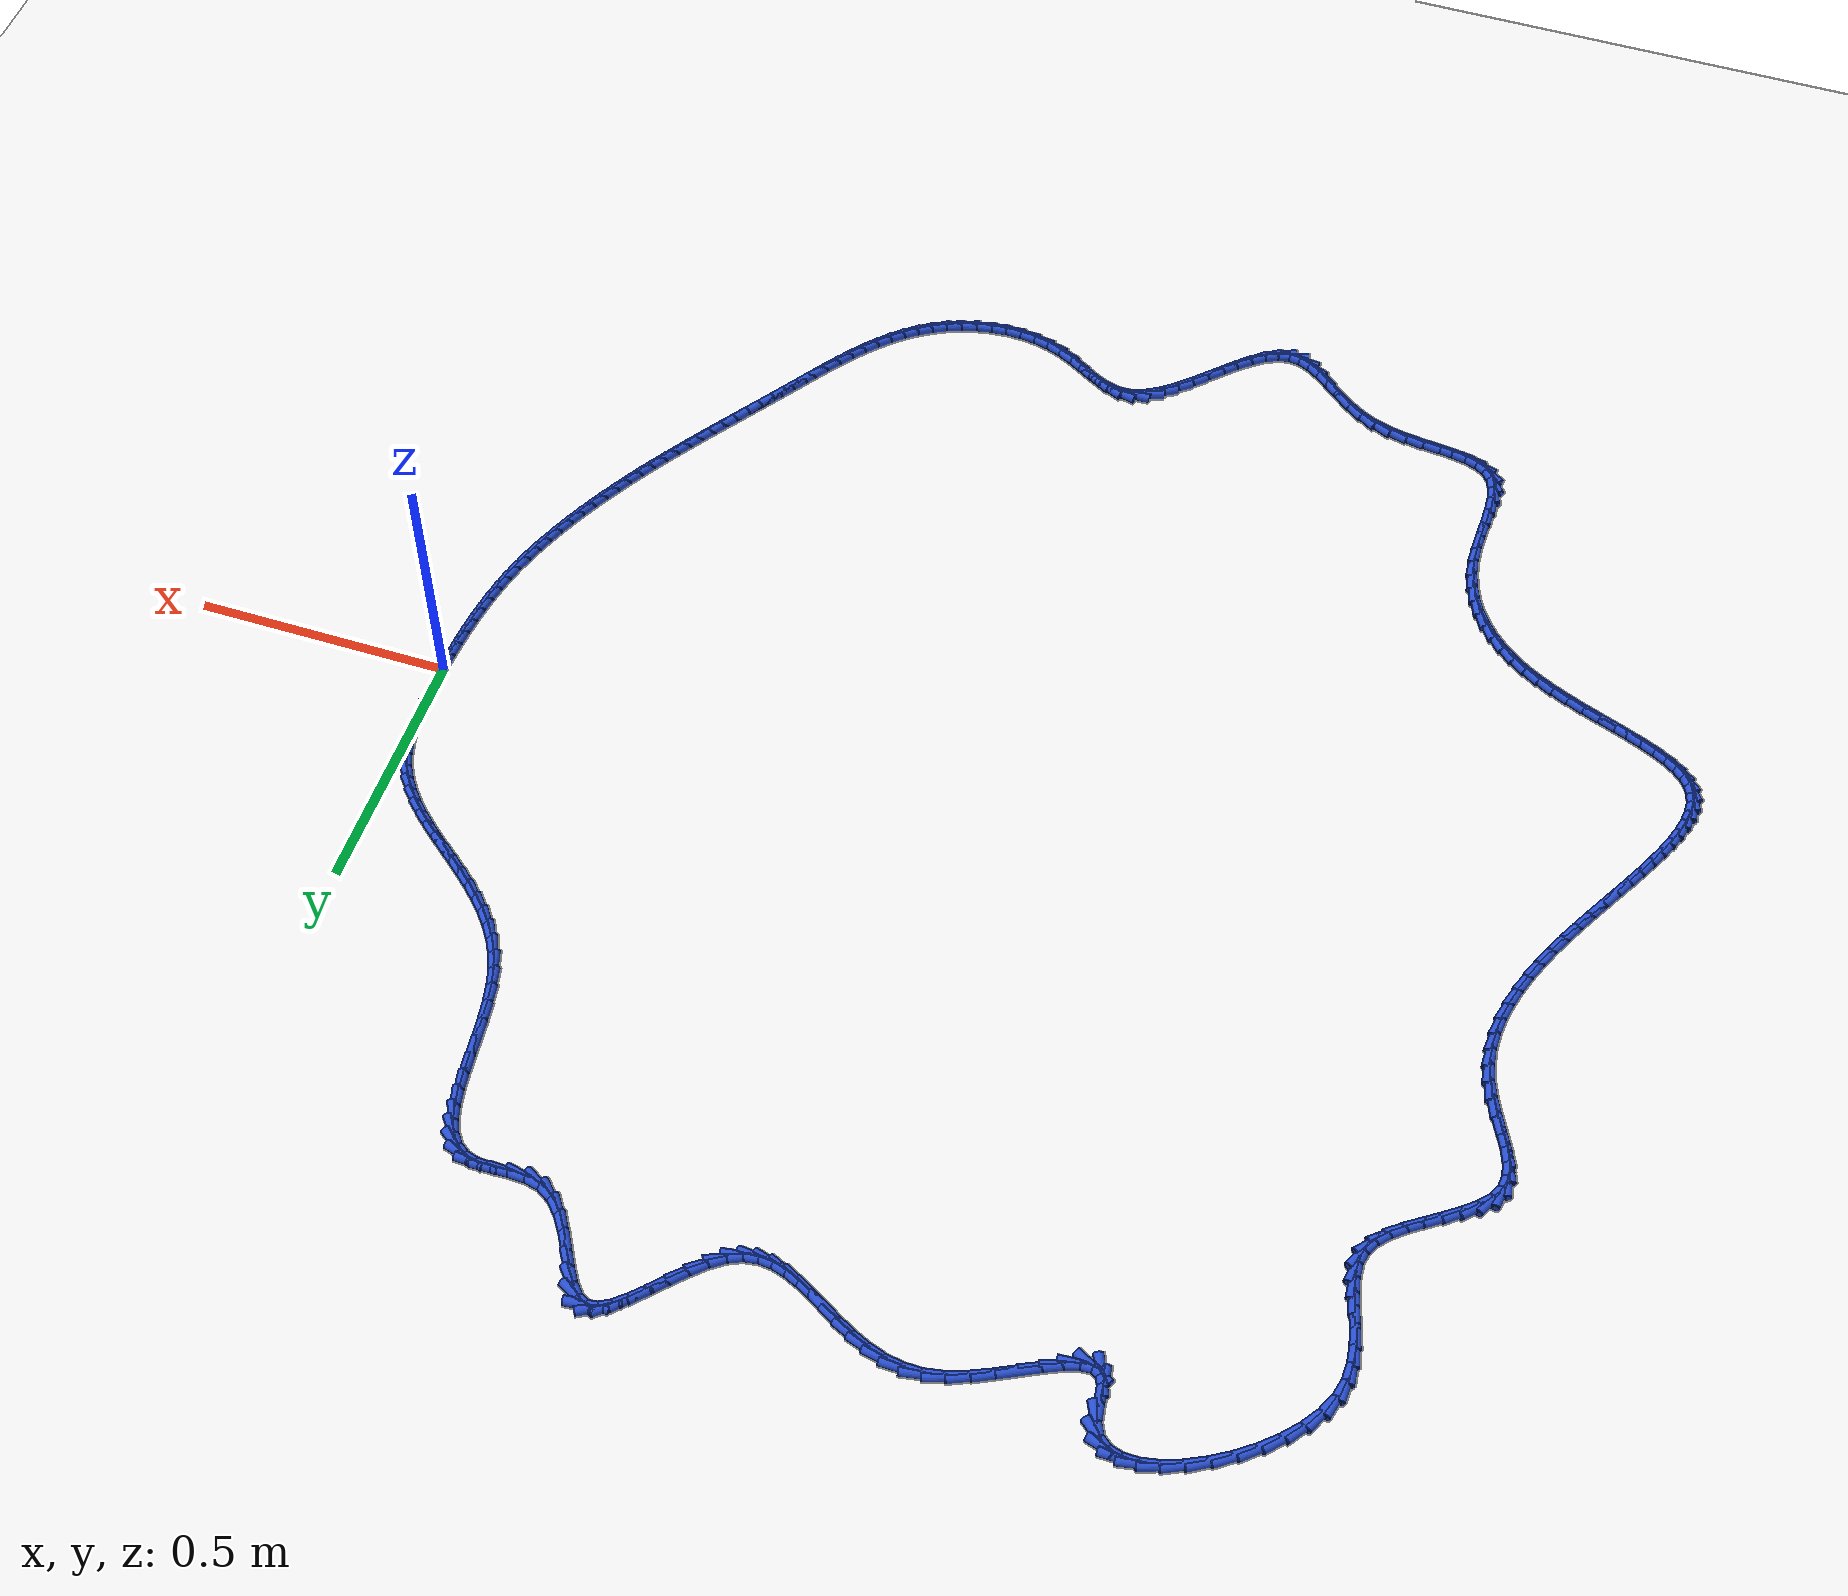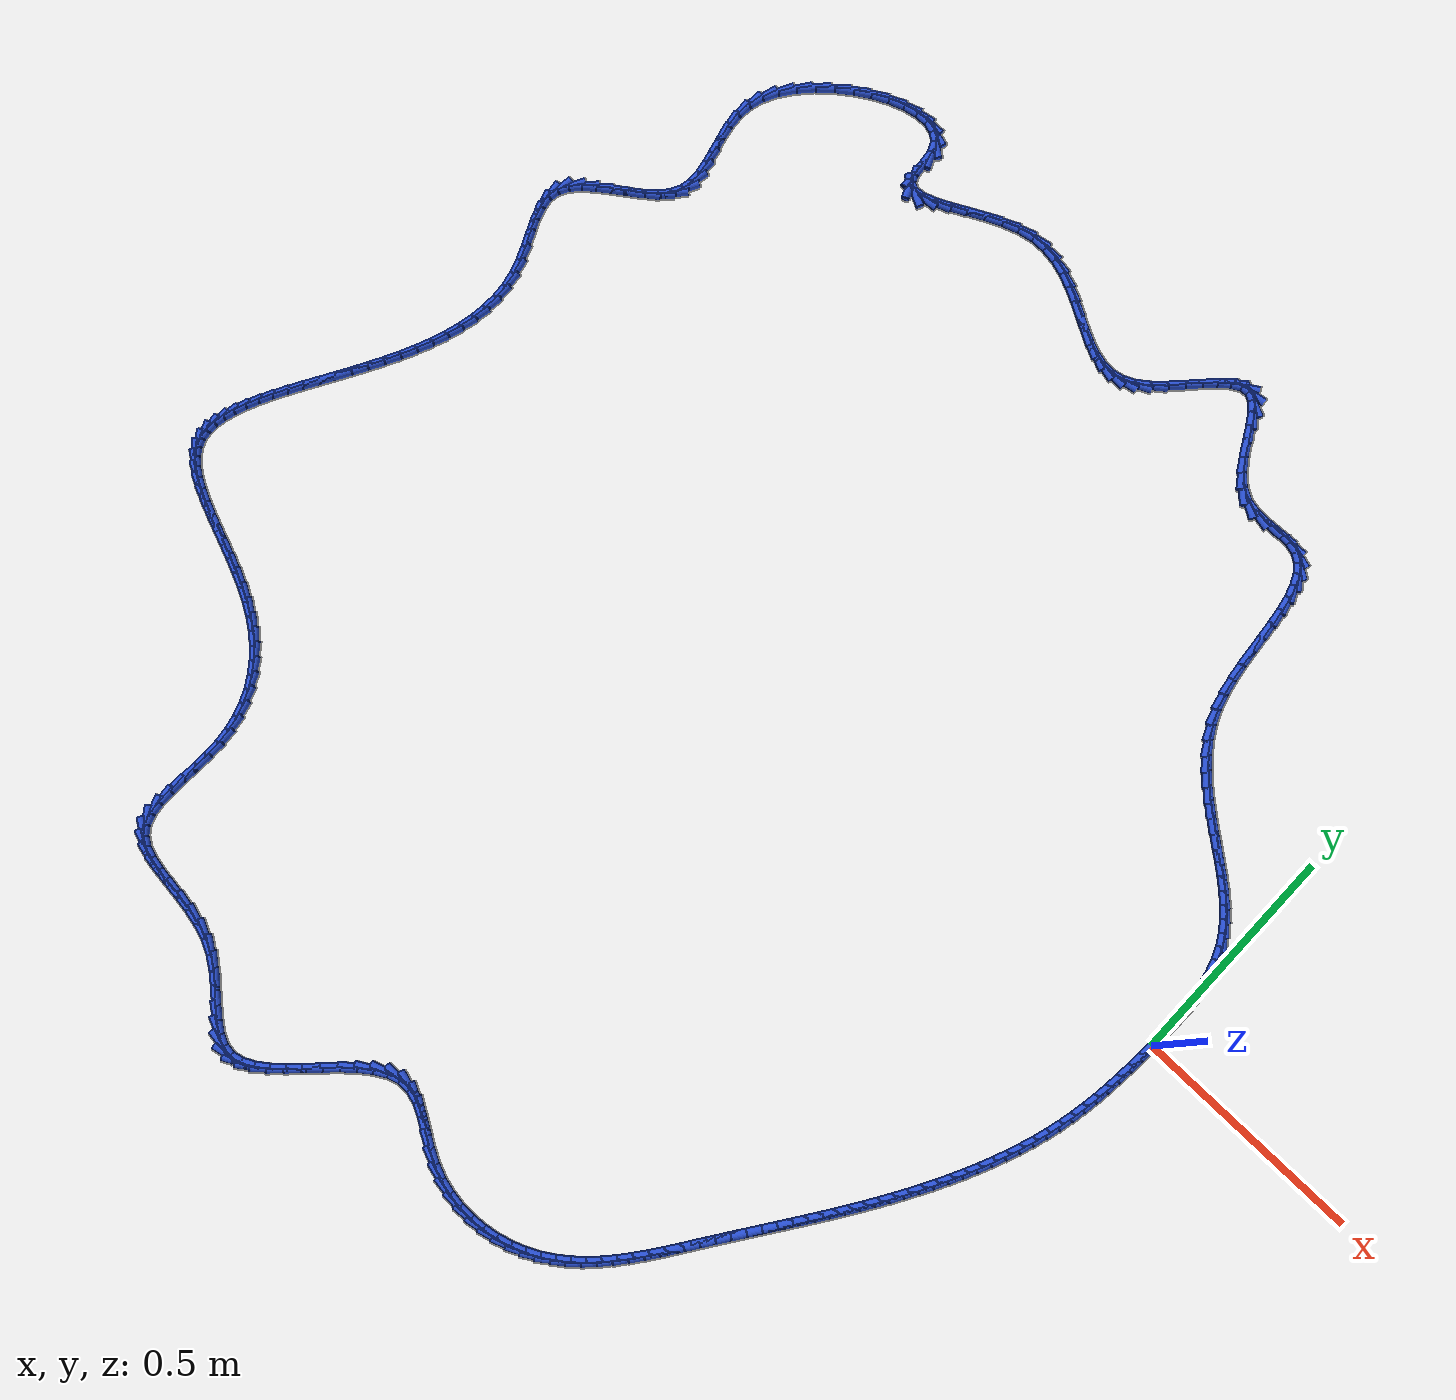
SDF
<sdf version="1.6">
 <world name="default">
  <light name="sun" type="directional">
   <pose>0 0 10 0 -0 0</pose>
   <diffuse>0.8 0.8 0.8 1</diffuse>
   <specular>0.2 0.2 0.2 1</specular>
   <attenuation>
    <range>1000</range>
    <constant>0.9</constant>
    <linear>0.01</linear>
    <quadratic>0.001</quadratic>
   </attenuation>
   <direction>-0.5 0.1 -0.9</direction>
  </light>
  <model name="ground_plane">
   <static>1</static>
   <link name="link">
    <collision name="collision">
     <geometry><plane><normal>0 0 1</normal><size>100 100</size></plane></geometry>
     <surface><friction><ode><mu>100</mu><mu2>50</mu2></ode></friction></surface>
    </collision>
    <visual name="visual">
     <cast_shadows>0</cast_shadows>
     <geometry><plane><normal>0 0 1</normal><size>100 100</size></plane></geometry>
     <material>
      <script><uri>file://media/materials/scripts/gazebo.material</uri><name>Gazebo/WhiteGlow</name></script>
     </material>
    </visual>
   </link>
  </model>
  <gravity>0 0 -9.8</gravity>
  <magnetic_field>6e-06 2.3e-05 -4.2e-05</magnetic_field>
  <atmosphere type="adiabatic"/>
  <physics name="default_physics" default="0" type="ode">
   <max_step_size>0.001</max_step_size>
   <real_time_factor>1</real_time_factor>
   <real_time_update_rate>1000</real_time_update_rate>
  </physics>
  <scene><ambient>0.4 0.4 0.4 1</ambient><background>0.7 0.7 0.7 1</background><shadows>1</shadows></scene>
  <spherical_coordinates>
   <surface_model>EARTH_WGS84</surface_model>
   <latitude_deg>0</latitude_deg>
   <longitude_deg>0</longitude_deg>
   <elevation>0</elevation>
   <heading_deg>0</heading_deg>
  </spherical_coordinates>
  <model name="line">
   <link name="link_0">
    <pose>1.6263032587282567e-19 -2.7755575615628914e-17 0.01 0 1.57 1.5383353069634973</pose>
    <collision name="collision">
     <geometry><cylinder><radius>0.01</radius><length>0.08</length></cylinder></geometry>
    </collision>
    <visual name="visual">
     <material>
      <script><name>Gazebo/Blue</name><uri>file://media/materials/scripts/gazebo.material</uri></script>
     </material>
     <geometry><cylinder><radius>0.01</radius><length>0.08</length></cylinder></geometry>
    </visual>
   </link>
   <link name="link_1">
    <pose>0.0010352555482330502 0.03188106552595872 0.01 0 1.57 1.560093773469132</pose>
    <collision name="collision">
     <geometry><cylinder><radius>0.01</radius><length>0.08</length></cylinder></geometry>
    </collision>
    <visual name="visual">
     <material>
      <script><name>Gazebo/Blue</name><uri>file://media/materials/scripts/gazebo.material</uri></script>
     </material>
     <geometry><cylinder><radius>0.01</radius><length>0.08</length></cylinder></geometry>
    </visual>
   </link>
   <link name="link_2">
    <pose>0.001378065888462798 0.06391054864702697 0.01 0 1.57 -1.5489534965763683</pose>
    <collision name="collision">
     <geometry><cylinder><radius>0.01</radius><length>0.08</length></cylinder></geometry>
    </collision>
    <visual name="visual">
     <material>
      <script><name>Gazebo/Blue</name><uri>file://media/materials/scripts/gazebo.material</uri></script>
     </material>
     <geometry><cylinder><radius>0.01</radius><length>0.08</length></cylinder></geometry>
    </visual>
   </link>
   <link name="link_3">
    <pose>0.0006816672699082812 0.09578773009873769 0.01 0 1.57 -1.504626500046836</pose>
    <collision name="collision">
     <geometry><cylinder><radius>0.01</radius><length>0.08</length></cylinder></geometry>
    </collision>
    <visual name="visual">
     <material>
      <script><name>Gazebo/Blue</name><uri>file://media/materials/scripts/gazebo.material</uri></script>
     </material>
     <geometry><cylinder><radius>0.01</radius><length>0.08</length></cylinder></geometry>
    </visual>
   </link>
   <link name="link_4">
    <pose>-0.001400704058211463 0.12721189061662377 0.01 0 1.57 -1.4470415365663511</pose>
    <collision name="collision">
     <geometry><cylinder><radius>0.01</radius><length>0.08</length></cylinder></geometry>
    </collision>
    <visual name="visual">
     <material>
      <script><name>Gazebo/Blue</name><uri>file://media/materials/scripts/gazebo.material</uri></script>
     </material>
     <geometry><cylinder><radius>0.01</radius><length>0.08</length></cylinder></geometry>
    </visual>
   </link>
   <link name="link_5">
    <pose>-0.005215811846677402 0.1578823109362181 0.01 0 1.57 -1.3743289784296675</pose>
    <collision name="collision">
     <geometry><cylinder><radius>0.01</radius><length>0.08</length></cylinder></geometry>
    </collision>
    <visual name="visual">
     <material>
      <script><name>Gazebo/Blue</name><uri>file://media/materials/scripts/gazebo.material</uri></script>
     </material>
     <geometry><cylinder><radius>0.01</radius><length>0.08</length></cylinder></geometry>
    </visual>
   </link>
   <link name="link_6">
    <pose>-0.011110419846270496 0.18749827179305362 0.01 0 1.57 -1.2844558011551233</pose>
    <collision name="collision">
     <geometry><cylinder><radius>0.01</radius><length>0.08</length></cylinder></geometry>
    </collision>
    <visual name="visual">
     <material>
      <script><name>Gazebo/Blue</name><uri>file://media/materials/scripts/gazebo.material</uri></script>
     </material>
     <geometry><cylinder><radius>0.01</radius><length>0.08</length></cylinder></geometry>
    </visual>
   </link>
   <link name="link_7">
    <pose>-0.019431291807771717 0.2157590539226632 0.01 0 1.57 -1.175740636228173</pose>
    <collision name="collision">
     <geometry><cylinder><radius>0.01</radius><length>0.08</length></cylinder></geometry>
    </collision>
    <visual name="visual">
     <material>
      <script><name>Gazebo/Blue</name><uri>file://media/materials/scripts/gazebo.material</uri></script>
     </material>
     <geometry><cylinder><radius>0.01</radius><length>0.08</length></cylinder></geometry>
    </visual>
   </link>
   <link name="link_8">
    <pose>-0.030524989544669867 0.24236410001326464 0.01 0 1.57 -1.0553115258710937</pose>
    <collision name="collision">
     <geometry><cylinder><radius>0.01</radius><length>0.08</length></cylinder></geometry>
    </collision>
    <visual name="visual">
     <material>
      <script><name>Gazebo/Blue</name><uri>file://media/materials/scripts/gazebo.material</uri></script>
     </material>
     <geometry><cylinder><radius>0.01</radius><length>0.08</length></cylinder></geometry>
    </visual>
   </link>
   <link name="link_9">
    <pose>-0.044567867071848406 0.2671493585449896 0.01 0 1.57 -0.946920727944196</pose>
    <collision name="collision">
     <geometry><cylinder><radius>0.01</radius><length>0.08</length></cylinder></geometry>
    </collision>
    <visual name="visual">
     <material>
      <script><name>Gazebo/Blue</name><uri>file://media/materials/scripts/gazebo.material</uri></script>
     </material>
     <geometry><cylinder><radius>0.01</radius><length>0.08</length></cylinder></geometry>
    </visual>
   </link>
   <link name="link_10">
    <pose>-0.06125665207494896 0.2903354358834038 0.01 0 1.57 -0.8569819977501223</pose>
    <collision name="collision">
     <geometry><cylinder><radius>0.01</radius><length>0.08</length></cylinder></geometry>
    </collision>
    <visual name="visual">
     <material>
      <script><name>Gazebo/Blue</name><uri>file://media/materials/scripts/gazebo.material</uri></script>
     </material>
     <geometry><cylinder><radius>0.01</radius><length>0.08</length></cylinder></geometry>
    </visual>
   </link>
   <link name="link_11">
    <pose>-0.08020420010105639 0.31221020342415334 0.01 0 1.57 -0.786169993335585</pose>
    <collision name="collision">
     <geometry><cylinder><radius>0.01</radius><length>0.08</length></cylinder></geometry>
    </collision>
    <visual name="visual">
     <material>
      <script><name>Gazebo/Blue</name><uri>file://media/materials/scripts/gazebo.material</uri></script>
     </material>
     <geometry><cylinder><radius>0.01</radius><length>0.08</length></cylinder></geometry>
    </visual>
   </link>
   <link name="link_12">
    <pose>-0.10102336669725559 0.3330615325628844 0.01 0 1.57 -0.7338665187570729</pose>
    <collision name="collision">
     <geometry><cylinder><radius>0.01</radius><length>0.08</length></cylinder></geometry>
    </collision>
    <visual name="visual">
     <material>
      <script><name>Gazebo/Blue</name><uri>file://media/materials/scripts/gazebo.material</uri></script>
     </material>
     <geometry><cylinder><radius>0.01</radius><length>0.08</length></cylinder></geometry>
    </visual>
   </link>
   <link name="link_13">
    <pose>-0.12332700741063148 0.3531772946952434 0.01 0 1.57 -0.6989416583695793</pose>
    <collision name="collision">
     <geometry><cylinder><radius>0.01</radius><length>0.08</length></cylinder></geometry>
    </collision>
    <visual name="visual">
     <material>
      <script><name>Gazebo/Blue</name><uri>file://media/materials/scripts/gazebo.material</uri></script>
     </material>
     <geometry><cylinder><radius>0.01</radius><length>0.08</length></cylinder></geometry>
    </visual>
   </link>
   <link name="link_14">
    <pose>-0.14672797778826902 0.3728453612168767 0.01 0 1.57 -0.6802627960401084</pose>
    <collision name="collision">
     <geometry><cylinder><radius>0.01</radius><length>0.08</length></cylinder></geometry>
    </collision>
    <visual name="visual">
     <material>
      <script><name>Gazebo/Blue</name><uri>file://media/materials/scripts/gazebo.material</uri></script>
     </material>
     <geometry><cylinder><radius>0.01</radius><length>0.08</length></cylinder></geometry>
    </visual>
   </link>
   <link name="link_15">
    <pose>-0.170839133377253 0.3923536035234307 0.01 0 1.57 -0.6769563162297912</pose>
    <collision name="collision">
     <geometry><cylinder><radius>0.01</radius><length>0.08</length></cylinder></geometry>
    </collision>
    <visual name="visual">
     <material>
      <script><name>Gazebo/Blue</name><uri>file://media/materials/scripts/gazebo.material</uri></script>
     </material>
     <geometry><cylinder><radius>0.01</radius><length>0.08</length></cylinder></geometry>
    </visual>
   </link>
   <link name="link_16">
    <pose>-0.19527332972466852 0.41198989301055144 0.01 0 1.57 -0.688501725564443</pose>
    <collision name="collision">
     <geometry><cylinder><radius>0.01</radius><length>0.08</length></cylinder></geometry>
    </collision>
    <visual name="visual">
     <material>
      <script><name>Gazebo/Blue</name><uri>file://media/materials/scripts/gazebo.material</uri></script>
     </material>
     <geometry><cylinder><radius>0.01</radius><length>0.08</length></cylinder></geometry>
    </visual>
   </link>
   <link name="link_17">
    <pose>-0.2196434223776003 0.4320421010738855 0.01 0 1.57 -0.7147190556229543</pose>
    <collision name="collision">
     <geometry><cylinder><radius>0.01</radius><length>0.08</length></cylinder></geometry>
    </collision>
    <visual name="visual">
     <material>
      <script><name>Gazebo/Blue</name><uri>file://media/materials/scripts/gazebo.material</uri></script>
     </material>
     <geometry><cylinder><radius>0.01</radius><length>0.08</length></cylinder></geometry>
    </visual>
   </link>
   <link name="link_18">
    <pose>-0.24356226688313337 0.45279809910907903 0.01 0 1.57 -0.755675742183482</pose>
    <collision name="collision">
     <geometry><cylinder><radius>0.01</radius><length>0.08</length></cylinder></geometry>
    </collision>
    <visual name="visual">
     <material>
      <script><name>Gazebo/Blue</name><uri>file://media/materials/scripts/gazebo.material</uri></script>
     </material>
     <geometry><cylinder><radius>0.01</radius><length>0.08</length></cylinder></geometry>
    </visual>
   </link>
   <link name="link_19">
    <pose>-0.2666427187883525 0.47454575851177827 0.01 0 1.57 -0.811511261096778</pose>
    <collision name="collision">
     <geometry><cylinder><radius>0.01</radius><length>0.08</length></cylinder></geometry>
    </collision>
    <visual name="visual">
     <material>
      <script><name>Gazebo/Blue</name><uri>file://media/materials/scripts/gazebo.material</uri></script>
     </material>
     <geometry><cylinder><radius>0.01</radius><length>0.08</length></cylinder></geometry>
    </visual>
   </link>
   <link name="link_20">
    <pose>-0.28849763364034275 0.49757295067762963 0.01 0 1.57 -0.8821661393426828</pose>
    <collision name="collision">
     <geometry><cylinder><radius>0.01</radius><length>0.08</length></cylinder></geometry>
    </collision>
    <visual name="visual">
     <material>
      <script><name>Gazebo/Blue</name><uri>file://media/materials/scripts/gazebo.material</uri></script>
     </material>
     <geometry><cylinder><radius>0.01</radius><length>0.08</length></cylinder></geometry>
    </visual>
   </link>
   <link name="link_21">
    <pose>-0.3087398669861889 0.5221675470022795 0.01 0 1.57 -0.9670183894623179</pose>
    <collision name="collision">
     <geometry><cylinder><radius>0.01</radius><length>0.08</length></cylinder></geometry>
    </collision>
    <visual name="visual">
     <material>
      <script><name>Gazebo/Blue</name><uri>file://media/materials/scripts/gazebo.material</uri></script>
     </material>
     <geometry><cylinder><radius>0.01</radius><length>0.08</length></cylinder></geometry>
    </visual>
   </link>
   <link name="link_22">
    <pose>-0.32698227437297595 0.5486174188813739 0.01 0 1.57 -1.0644885234339185</pose>
    <collision name="collision">
     <geometry><cylinder><radius>0.01</radius><length>0.08</length></cylinder></geometry>
    </collision>
    <visual name="visual">
     <material>
      <script><name>Gazebo/Blue</name><uri>file://media/materials/scripts/gazebo.material</uri></script>
     </material>
     <geometry><cylinder><radius>0.01</radius><length>0.08</length></cylinder></geometry>
    </visual>
   </link>
   <link name="link_23">
    <pose>-0.3428377113477887 0.5772104377105595 0.01 0 1.57 -1.171765569708447</pose>
    <collision name="collision">
     <geometry><cylinder><radius>0.01</radius><length>0.08</length></cylinder></geometry>
    </collision>
    <visual name="visual">
     <material>
      <script><name>Gazebo/Blue</name><uri>file://media/materials/scripts/gazebo.material</uri></script>
     </material>
     <geometry><cylinder><radius>0.01</radius><length>0.08</length></cylinder></geometry>
    </visual>
   </link>
   <link name="link_24">
    <pose>-0.35591903345771225 0.6082344748854823 0.01 0 1.57 -1.2799683563777309</pose>
    <collision name="collision">
     <geometry><cylinder><radius>0.01</radius><length>0.08</length></cylinder></geometry>
    </collision>
    <visual name="visual">
     <material>
      <script><name>Gazebo/Blue</name><uri>file://media/materials/scripts/gazebo.material</uri></script>
     </material>
     <geometry><cylinder><radius>0.01</radius><length>0.08</length></cylinder></geometry>
    </visual>
   </link>
   <link name="link_25">
    <pose>-0.3659776025540326 0.6418398030833943 0.01 0 1.57 -1.3636214379125997</pose>
    <collision name="collision">
     <geometry><cylinder><radius>0.01</radius><length>0.08</length></cylinder></geometry>
    </collision>
    <visual name="visual">
     <material>
      <script><name>Gazebo/Blue</name><uri>file://media/materials/scripts/gazebo.material</uri></script>
     </material>
     <geometry><cylinder><radius>0.01</radius><length>0.08</length></cylinder></geometry>
    </visual>
   </link>
   <link name="link_26">
    <pose>-0.37346836378134174 0.6774777220358674 0.01 0 1.57 -1.420165587430014</pose>
    <collision name="collision">
     <geometry><cylinder><radius>0.01</radius><length>0.08</length></cylinder></geometry>
    </collision>
    <visual name="visual">
     <material>
      <script><name>Gazebo/Blue</name><uri>file://media/materials/scripts/gazebo.material</uri></script>
     </material>
     <geometry><cylinder><radius>0.01</radius><length>0.08</length></cylinder></geometry>
    </visual>
   </link>
   <link name="link_27">
    <pose>-0.37906912351903477 0.7143781305753185 0.01 0 1.57 -1.453964266465154</pose>
    <collision name="collision">
     <geometry><cylinder><radius>0.01</radius><length>0.08</length></cylinder></geometry>
    </collision>
    <visual name="visual">
     <material>
      <script><name>Gazebo/Blue</name><uri>file://media/materials/scripts/gazebo.material</uri></script>
     </material>
     <geometry><cylinder><radius>0.01</radius><length>0.08</length></cylinder></geometry>
    </visual>
   </link>
   <link name="link_28">
    <pose>-0.38345777690040506 0.7517708393618422 0.01 0 1.57 -1.4673154478947013</pose>
    <collision name="collision">
     <geometry><cylinder><radius>0.01</radius><length>0.08</length></cylinder></geometry>
    </collision>
    <visual name="visual">
     <material>
      <script><name>Gazebo/Blue</name><uri>file://media/materials/scripts/gazebo.material</uri></script>
     </material>
     <geometry><cylinder><radius>0.01</radius><length>0.08</length></cylinder></geometry>
    </visual>
   </link>
   <link name="link_29">
    <pose>-0.3873122190587464 0.7888856590555314 0.01 0 1.57 -1.4603935394240113</pose>
    <collision name="collision">
     <geometry><cylinder><radius>0.01</radius><length>0.08</length></cylinder></geometry>
    </collision>
    <visual name="visual">
     <material>
      <script><name>Gazebo/Blue</name><uri>file://media/materials/scripts/gazebo.material</uri></script>
     </material>
     <geometry><cylinder><radius>0.01</radius><length>0.08</length></cylinder></geometry>
    </visual>
   </link>
   <link name="link_30">
    <pose>-0.39131034512735235 0.8249524003164805 0.01 0 1.57 -1.4309868540042958</pose>
    <collision name="collision">
     <geometry><cylinder><radius>0.01</radius><length>0.08</length></cylinder></geometry>
    </collision>
    <visual name="visual">
     <material>
      <script><name>Gazebo/Blue</name><uri>file://media/materials/scripts/gazebo.material</uri></script>
     </material>
     <geometry><cylinder><radius>0.01</radius><length>0.08</length></cylinder></geometry>
    </visual>
   </link>
   <link name="link_31">
    <pose>-0.3961300502395162 0.8592008738047826 0.01 0 1.57 -1.3737902713503496</pose>
    <collision name="collision">
     <geometry><cylinder><radius>0.01</radius><length>0.08</length></cylinder></geometry>
    </collision>
    <visual name="visual">
     <material>
      <script><name>Gazebo/Blue</name><uri>file://media/materials/scripts/gazebo.material</uri></script>
     </material>
     <geometry><cylinder><radius>0.01</radius><length>0.08</length></cylinder></geometry>
    </visual>
   </link>
   <link name="link_32">
    <pose>-0.4024492295285319 0.8908608901805314 0.01 0 1.57 -1.2791405840011714</pose>
    <collision name="collision">
     <geometry><cylinder><radius>0.01</radius><length>0.08</length></cylinder></geometry>
    </collision>
    <visual name="visual">
     <material>
      <script><name>Gazebo/Blue</name><uri>file://media/materials/scripts/gazebo.material</uri></script>
     </material>
     <geometry><cylinder><radius>0.01</radius><length>0.08</length></cylinder></geometry>
    </visual>
   </link>
   <link name="link_33">
    <pose>-0.41094577812769273 0.9191622601038207 0.01 0 1.57 -1.1317498638830485</pose>
    <collision name="collision">
     <geometry><cylinder><radius>0.01</radius><length>0.08</length></cylinder></geometry>
    </collision>
    <visual name="visual">
     <material>
      <script><name>Gazebo/Blue</name><uri>file://media/materials/scripts/gazebo.material</uri></script>
     </material>
     <geometry><cylinder><radius>0.01</radius><length>0.08</length></cylinder></geometry>
    </visual>
   </link>
   <link name="link_34">
    <pose>-0.42229759117029253 0.9433347942347444 0.01 0 1.57 -0.9131739533886902</pose>
    <collision name="collision">
     <geometry><cylinder><radius>0.01</radius><length>0.08</length></cylinder></geometry>
    </collision>
    <visual name="visual">
     <material>
      <script><name>Gazebo/Blue</name><uri>file://media/materials/scripts/gazebo.material</uri></script>
     </material>
     <geometry><cylinder><radius>0.01</radius><length>0.08</length></cylinder></geometry>
    </visual>
   </link>
   <link name="link_35">
    <pose>-0.4371825637896247 0.9626083032333959 0.01 0 1.57 -0.6190096114699019</pose>
    <collision name="collision">
     <geometry><cylinder><radius>0.01</radius><length>0.08</length></cylinder></geometry>
    </collision>
    <visual name="visual">
     <material>
      <script><name>Gazebo/Blue</name><uri>file://media/materials/scripts/gazebo.material</uri></script>
     </material>
     <geometry><cylinder><radius>0.01</radius><length>0.08</length></cylinder></geometry>
    </visual>
   </link>
   <link name="link_36">
    <pose>-0.45627859111898295 0.9762125977598689 0.01 0 1.57 -0.2904046029503048</pose>
    <collision name="collision">
     <geometry><cylinder><radius>0.01</radius><length>0.08</length></cylinder></geometry>
    </collision>
    <visual name="visual">
     <material>
      <script><name>Gazebo/Blue</name><uri>file://media/materials/scripts/gazebo.material</uri></script>
     </material>
     <geometry><cylinder><radius>0.01</radius><length>0.08</length></cylinder></geometry>
    </visual>
   </link>
   <link name="link_37">
    <pose>-0.4802619861468897 0.983380118651616 0.01 0 1.57 -0.041829468330891004</pose>
    <collision name="collision">
     <geometry><cylinder><radius>0.01</radius><length>0.08</length></cylinder></geometry>
    </collision>
    <visual name="visual">
     <material>
      <script><name>Gazebo/Blue</name><uri>file://media/materials/scripts/gazebo.material</uri></script>
     </material>
     <geometry><cylinder><radius>0.01</radius><length>0.08</length></cylinder></geometry>
    </visual>
   </link>
   <link name="link_38">
    <pose>-0.5090618361465976 0.9845855041699224 0.01 0 1.57 0.03351676105892445</pose>
    <collision name="collision">
     <geometry><cylinder><radius>0.01</radius><length>0.08</length></cylinder></geometry>
    </collision>
    <visual name="visual">
     <material>
      <script><name>Gazebo/Blue</name><uri>file://media/materials/scripts/gazebo.material</uri></script>
     </material>
     <geometry><cylinder><radius>0.01</radius><length>0.08</length></cylinder></geometry>
    </visual>
   </link>
   <link name="link_39">
    <pose>-0.5406688712487268 0.9835257418606829 0.01 0 1.57 -0.027654187509504276</pose>
    <collision name="collision">
     <geometry><cylinder><radius>0.01</radius><length>0.08</length></cylinder></geometry>
    </collision>
    <visual name="visual">
     <material>
      <script><name>Gazebo/Blue</name><uri>file://media/materials/scripts/gazebo.material</uri></script>
     </material>
     <geometry><cylinder><radius>0.01</radius><length>0.08</length></cylinder></geometry>
    </visual>
   </link>
   <link name="link_40">
    <pose>-0.5727636081067112 0.9844135220545379 0.01 0 1.57 -0.22881374933406928</pose>
    <collision name="collision">
     <geometry><cylinder><radius>0.01</radius><length>0.08</length></cylinder></geometry>
    </collision>
    <visual name="visual">
     <material>
      <script><name>Gazebo/Blue</name><uri>file://media/materials/scripts/gazebo.material</uri></script>
     </material>
     <geometry><cylinder><radius>0.01</radius><length>0.08</length></cylinder></geometry>
    </visual>
   </link>
   <link name="link_41">
    <pose>-0.6030265633739852 0.9914615350821276 0.01 0 1.57 -0.5541904445779866</pose>
    <collision name="collision">
     <geometry><cylinder><radius>0.01</radius><length>0.08</length></cylinder></geometry>
    </collision>
    <visual name="visual">
     <material>
      <script><name>Gazebo/Blue</name><uri>file://media/materials/scripts/gazebo.material</uri></script>
     </material>
     <geometry><cylinder><radius>0.01</radius><length>0.08</length></cylinder></geometry>
    </visual>
   </link>
   <link name="link_42">
    <pose>-0.6295690195899953 1.0078882822779218 0.01 0 1.57 -0.8125869228990091</pose>
    <collision name="collision">
     <geometry><cylinder><radius>0.01</radius><length>0.08</length></cylinder></geometry>
    </collision>
    <visual name="visual">
     <material>
      <script><name>Gazebo/Blue</name><uri>file://media/materials/scripts/gazebo.material</uri></script>
     </material>
     <geometry><cylinder><radius>0.01</radius><length>0.08</length></cylinder></geometry>
    </visual>
   </link>
   <link name="link_43">
    <pose>-0.652559514438857 1.0321642092608283 0.01 0 1.57 -0.9648073413728792</pose>
    <collision name="collision">
     <geometry><cylinder><radius>0.01</radius><length>0.08</length></cylinder></geometry>
    </collision>
    <visual name="visual">
     <material>
      <script><name>Gazebo/Blue</name><uri>file://media/materials/scripts/gazebo.material</uri></script>
     </material>
     <geometry><cylinder><radius>0.01</radius><length>0.08</length></cylinder></geometry>
    </visual>
   </link>
   <link name="link_44">
    <pose>-0.6727800432870837 1.061343927905111 0.01 0 1.57 -1.0410724566464922</pose>
    <collision name="collision">
     <geometry><cylinder><radius>0.01</radius><length>0.08</length></cylinder></geometry>
    </collision>
    <visual name="visual">
     <material>
      <script><name>Gazebo/Blue</name><uri>file://media/materials/scripts/gazebo.material</uri></script>
     </material>
     <geometry><cylinder><radius>0.01</radius><length>0.08</length></cylinder></geometry>
    </visual>
   </link>
   <link name="link_45">
    <pose>-0.691012707511905 1.092481805416899 0.01 0 1.57 -1.056712876413495</pose>
    <collision name="collision">
     <geometry><cylinder><radius>0.01</radius><length>0.08</length></cylinder></geometry>
    </collision>
    <visual name="visual">
     <material>
      <script><name>Gazebo/Blue</name><uri>file://media/materials/scripts/gazebo.material</uri></script>
     </material>
     <geometry><cylinder><radius>0.01</radius><length>0.08</length></cylinder></geometry>
    </visual>
   </link>
   <link name="link_46">
    <pose>-0.7080396084905498 1.1226322090023217 0.01 0 1.57 -1.0062554882138028</pose>
    <collision name="collision">
     <geometry><cylinder><radius>0.01</radius><length>0.08</length></cylinder></geometry>
    </collision>
    <visual name="visual">
     <material>
      <script><name>Gazebo/Blue</name><uri>file://media/materials/scripts/gazebo.material</uri></script>
     </material>
     <geometry><cylinder><radius>0.01</radius><length>0.08</length></cylinder></geometry>
    </visual>
   </link>
   <link name="link_47">
    <pose>-0.7246428476002467 1.1488495058675068 0.01 0 1.57 -0.8507831532123473</pose>
    <collision name="collision">
     <geometry><cylinder><radius>0.01</radius><length>0.08</length></cylinder></geometry>
    </collision>
    <visual name="visual">
     <material>
      <script><name>Gazebo/Blue</name><uri>file://media/materials/scripts/gazebo.material</uri></script>
     </material>
     <geometry><cylinder><radius>0.01</radius><length>0.08</length></cylinder></geometry>
    </visual>
   </link>
   <link name="link_48">
    <pose>-0.7416045262182246 1.1681880632185835 0.01 0 1.57 -0.4839188857858722</pose>
    <collision name="collision">
     <geometry><cylinder><radius>0.01</radius><length>0.08</length></cylinder></geometry>
    </collision>
    <visual name="visual">
     <material>
      <script><name>Gazebo/Blue</name><uri>file://media/materials/scripts/gazebo.material</uri></script>
     </material>
     <geometry><cylinder><radius>0.01</radius><length>0.08</length></cylinder></geometry>
    </visual>
   </link>
   <link name="link_49">
    <pose>-0.7597066811475539 1.1777025938008612 0.01 0 1.57 0.10765609307942972</pose>
    <collision name="collision">
     <geometry><cylinder><radius>0.01</radius><length>0.08</length></cylinder></geometry>
    </collision>
    <visual name="visual">
     <material>
      <script><name>Gazebo/Blue</name><uri>file://media/materials/scripts/gazebo.material</uri></script>
     </material>
     <geometry><cylinder><radius>0.01</radius><length>0.08</length></cylinder></geometry>
    </visual>
   </link>
   <link name="link_50">
    <pose>-0.7795233299417831 1.175560930573153 0.01 0 1.57 0.5119483099922227</pose>
    <collision name="collision">
     <geometry><cylinder><radius>0.01</radius><length>0.08</length></cylinder></geometry>
    </collision>
    <visual name="visual">
     <material>
      <script><name>Gazebo/Blue</name><uri>file://media/materials/scripts/gazebo.material</uri></script>
     </material>
     <geometry><cylinder><radius>0.01</radius><length>0.08</length></cylinder></geometry>
    </visual>
   </link>
   <link name="link_51">
    <pose>-0.8009584918633995 1.1635160970115264 0.01 0 1.57 0.7063978190612228</pose>
    <collision name="collision">
     <geometry><cylinder><radius>0.01</radius><length>0.08</length></cylinder></geometry>
    </collision>
    <visual name="visual">
     <material>
      <script><name>Gazebo/Blue</name><uri>file://media/materials/scripts/gazebo.material</uri></script>
     </material>
     <geometry><cylinder><radius>0.01</radius><length>0.08</length></cylinder></geometry>
    </visual>
   </link>
   <link name="link_52">
    <pose>-0.8237815558473549 1.1440415294349666 0.01 0 1.57 0.7947038013231421</pose>
    <collision name="collision">
     <geometry><cylinder><radius>0.01</radius><length>0.08</length></cylinder></geometry>
    </collision>
    <visual name="visual">
     <material>
      <script><name>Gazebo/Blue</name><uri>file://media/materials/scripts/gazebo.material</uri></script>
     </material>
     <geometry><cylinder><radius>0.01</radius><length>0.08</length></cylinder></geometry>
    </visual>
   </link>
   <link name="link_53">
    <pose>-0.8477619108286011 1.1196106641624588 0.01 0 1.57 0.8241025272228049</pose>
    <collision name="collision">
     <geometry><cylinder><radius>0.01</radius><length>0.08</length></cylinder></geometry>
    </collision>
    <visual name="visual">
     <material>
      <script><name>Gazebo/Blue</name><uri>file://media/materials/scripts/gazebo.material</uri></script>
     </material>
     <geometry><cylinder><radius>0.01</radius><length>0.08</length></cylinder></geometry>
    </visual>
   </link>
   <link name="link_54">
    <pose>-0.8726689457420906 1.0926969375129894 0.01 0 1.57 0.8105240764414253</pose>
    <collision name="collision">
     <geometry><cylinder><radius>0.01</radius><length>0.08</length></cylinder></geometry>
    </collision>
    <visual name="visual">
     <material>
      <script><name>Gazebo/Blue</name><uri>file://media/materials/scripts/gazebo.material</uri></script>
     </material>
     <geometry><cylinder><radius>0.01</radius><length>0.08</length></cylinder></geometry>
    </visual>
   </link>
   <link name="link_55">
    <pose>-0.8982720495227755 1.0657737858055436 0.01 0 1.57 0.7535566761562176</pose>
    <collision name="collision">
     <geometry><cylinder><radius>0.01</radius><length>0.08</length></cylinder></geometry>
    </collision>
    <visual name="visual">
     <material>
      <script><name>Gazebo/Blue</name><uri>file://media/materials/scripts/gazebo.material</uri></script>
     </material>
     <geometry><cylinder><radius>0.01</radius><length>0.08</length></cylinder></geometry>
    </visual>
   </link>
   <link name="link_56">
    <pose>-0.9243406111056073 1.0413146453591071 0.01 0 1.57 0.6384733091120199</pose>
    <collision name="collision">
     <geometry><cylinder><radius>0.01</radius><length>0.08</length></cylinder></geometry>
    </collision>
    <visual name="visual">
     <material>
      <script><name>Gazebo/Blue</name><uri>file://media/materials/scripts/gazebo.material</uri></script>
     </material>
     <geometry><cylinder><radius>0.01</radius><length>0.08</length></cylinder></geometry>
    </visual>
   </link>
   <link name="link_57">
    <pose>-0.950644019425538 1.0217929524926654 0.01 0 1.57 0.4342787155163912</pose>
    <collision name="collision">
     <geometry><cylinder><radius>0.01</radius><length>0.08</length></cylinder></geometry>
    </collision>
    <visual name="visual">
     <material>
      <script><name>Gazebo/Blue</name><uri>file://media/materials/scripts/gazebo.material</uri></script>
     </material>
     <geometry><cylinder><radius>0.01</radius><length>0.08</length></cylinder></geometry>
    </visual>
   </link>
   <link name="link_58">
    <pose>-0.9769611053597728 1.0095868272610382 0.01 0 1.57 0.16494484447527724</pose>
    <collision name="collision">
     <geometry><cylinder><radius>0.01</radius><length>0.08</length></cylinder></geometry>
    </collision>
    <visual name="visual">
     <material>
      <script><name>Gazebo/Blue</name><uri>file://media/materials/scripts/gazebo.material</uri></script>
     </material>
     <geometry><cylinder><radius>0.01</radius><length>0.08</length></cylinder></geometry>
    </visual>
   </link>
   <link name="link_59">
    <pose>-1.0032553889905436 1.0052099549888966 0.01 0 1.57 -0.08566554288172233</pose>
    <collision name="collision">
     <geometry><cylinder><radius>0.01</radius><length>0.08</length></cylinder></geometry>
    </collision>
    <visual name="visual">
     <material>
      <script><name>Gazebo/Blue</name><uri>file://media/materials/scripts/gazebo.material</uri></script>
     </material>
     <geometry><cylinder><radius>0.01</radius><length>0.08</length></cylinder></geometry>
    </visual>
   </link>
   <link name="link_60">
    <pose>-1.0296586587412213 1.007477354643281 0.01 0 1.57 -0.2800429669759666</pose>
    <collision name="collision">
     <geometry><cylinder><radius>0.01</radius><length>0.08</length></cylinder></geometry>
    </collision>
    <visual name="visual">
     <material>
      <script><name>Gazebo/Blue</name><uri>file://media/materials/scripts/gazebo.material</uri></script>
     </material>
     <geometry><cylinder><radius>0.01</radius><length>0.08</length></cylinder></geometry>
    </visual>
   </link>
   <link name="link_61">
    <pose>-1.0563088518758008 1.015141972738158 0.01 0 1.57 -0.41200512017393365</pose>
    <collision name="collision">
     <geometry><cylinder><radius>0.01</radius><length>0.08</length></cylinder></geometry>
    </collision>
    <visual name="visual">
     <material>
      <script><name>Gazebo/Blue</name><uri>file://media/materials/scripts/gazebo.material</uri></script>
     </material>
     <geometry><cylinder><radius>0.01</radius><length>0.08</length></cylinder></geometry>
    </visual>
   </link>
   <link name="link_62">
    <pose>-1.0833439056582777 1.0269567557874957 0.01 0 1.57 -0.4905327318039381</pose>
    <collision name="collision">
     <geometry><cylinder><radius>0.01</radius><length>0.08</length></cylinder></geometry>
    </collision>
    <visual name="visual">
     <material>
      <script><name>Gazebo/Blue</name><uri>file://media/materials/scripts/gazebo.material</uri></script>
     </material>
     <geometry><cylinder><radius>0.01</radius><length>0.08</length></cylinder></geometry>
    </visual>
   </link>
   <link name="link_63">
    <pose>-1.1109017573526472 1.041674650305261 0.01 0 1.57 -0.5257739572577095</pose>
    <collision name="collision">
     <geometry><cylinder><radius>0.01</radius><length>0.08</length></cylinder></geometry>
    </collision>
    <visual name="visual">
     <material>
      <script><name>Gazebo/Blue</name><uri>file://media/materials/scripts/gazebo.material</uri></script>
     </material>
     <geometry><cylinder><radius>0.01</radius><length>0.08</length></cylinder></geometry>
    </visual>
   </link>
   <link name="link_64">
    <pose>-1.1391203442229048 1.0580486028054217 0.01 0 1.57 -0.5243695558374367</pose>
    <collision name="collision">
     <geometry><cylinder><radius>0.01</radius><length>0.08</length></cylinder></geometry>
    </collision>
    <visual name="visual">
     <material>
      <script><name>Gazebo/Blue</name><uri>file://media/materials/scripts/gazebo.material</uri></script>
     </material>
     <geometry><cylinder><radius>0.01</radius><length>0.08</length></cylinder></geometry>
    </visual>
   </link>
   <link name="link_65">
    <pose>-1.1681376035330462 1.0748315598019451 0.01 0 1.57 -0.4891645409560779</pose>
    <collision name="collision">
     <geometry><cylinder><radius>0.01</radius><length>0.08</length></cylinder></geometry>
    </collision>
    <visual name="visual">
     <material>
      <script><name>Gazebo/Blue</name><uri>file://media/materials/scripts/gazebo.material</uri></script>
     </material>
     <geometry><cylinder><radius>0.01</radius><length>0.08</length></cylinder></geometry>
    </visual>
   </link>
   <link name="link_66">
    <pose>-1.1980914725470666 1.0907764678087983 0.01 0 1.57 -0.420090462002091</pose>
    <collision name="collision">
     <geometry><cylinder><radius>0.01</radius><length>0.08</length></cylinder></geometry>
    </collision>
    <visual name="visual">
     <material>
      <script><name>Gazebo/Blue</name><uri>file://media/materials/scripts/gazebo.material</uri></script>
     </material>
     <geometry><cylinder><radius>0.01</radius><length>0.08</length></cylinder></geometry>
    </visual>
   </link>
   <link name="link_67">
    <pose>-1.2291198885289614 1.1046362733399493 0.01 0 1.57 -0.31561590541470685</pose>
    <collision name="collision">
     <geometry><cylinder><radius>0.01</radius><length>0.08</length></cylinder></geometry>
    </collision>
    <visual name="visual">
     <material>
      <script><name>Gazebo/Blue</name><uri>file://media/materials/scripts/gazebo.material</uri></script>
     </material>
     <geometry><cylinder><radius>0.01</radius><length>0.08</length></cylinder></geometry>
    </visual>
   </link>
   <link name="link_68">
    <pose>-1.2613607887427254 1.1151639229093648 0.01 0 1.57 -0.1752657092987587</pose>
    <collision name="collision">
     <geometry><cylinder><radius>0.01</radius><length>0.08</length></cylinder></geometry>
    </collision>
    <visual name="visual">
     <material>
      <script><name>Gazebo/Blue</name><uri>file://media/materials/scripts/gazebo.material</uri></script>
     </material>
     <geometry><cylinder><radius>0.01</radius><length>0.08</length></cylinder></geometry>
    </visual>
   </link>
   <link name="link_69">
    <pose>-1.2949521104523547 1.121112363031013 0.01 0 1.57 -0.0034828337146663407</pose>
    <collision name="collision">
     <geometry><cylinder><radius>0.01</radius><length>0.08</length></cylinder></geometry>
    </collision>
    <visual name="visual">
     <material>
      <script><name>Gazebo/Blue</name><uri>file://media/materials/scripts/gazebo.material</uri></script>
     </material>
     <geometry><cylinder><radius>0.01</radius><length>0.08</length></cylinder></geometry>
    </visual>
   </link>
   <link name="link_70">
    <pose>-1.3300317909218455 1.1212345402188606 0.01 0 1.57 0.1841056616848136</pose>
    <collision name="collision">
     <geometry><cylinder><radius>0.01</radius><length>0.08</length></cylinder></geometry>
    </collision>
    <visual name="visual">
     <material>
      <script><name>Gazebo/Blue</name><uri>file://media/materials/scripts/gazebo.material</uri></script>
     </material>
     <geometry><cylinder><radius>0.01</radius><length>0.08</length></cylinder></geometry>
    </visual>
   </link>
   <link name="link_71">
    <pose>-1.366696831865767 1.1144069839541586 0.01 0 1.57 0.33178543731628474</pose>
    <collision name="collision">
     <geometry><cylinder><radius>0.01</radius><length>0.08</length></cylinder></geometry>
    </collision>
    <visual name="visual">
     <material>
      <script><name>Gazebo/Blue</name><uri>file://media/materials/scripts/gazebo.material</uri></script>
     </material>
     <geometry><cylinder><radius>0.01</radius><length>0.08</length></cylinder></geometry>
    </visual>
   </link>
   <link name="link_72">
    <pose>-1.404412599082707 1.1014131100758102 0.01 0 1.57 0.4205974914448263</pose>
    <collision name="collision">
     <geometry><cylinder><radius>0.01</radius><length>0.08</length></cylinder></geometry>
    </collision>
    <visual name="visual">
     <material>
      <script><name>Gazebo/Blue</name><uri>file://media/materials/scripts/gazebo.material</uri></script>
     </material>
     <geometry><cylinder><radius>0.01</radius><length>0.08</length></cylinder></geometry>
    </visual>
   </link>
   <link name="link_73">
    <pose>-1.442148256166399 1.0845343512250025 0.01 0 1.57 0.46552470300874693</pose>
    <collision name="collision">
     <geometry><cylinder><radius>0.01</radius><length>0.08</length></cylinder></geometry>
    </collision>
    <visual name="visual">
     <material>
      <script><name>Gazebo/Blue</name><uri>file://media/materials/scripts/gazebo.material</uri></script>
     </material>
     <geometry><cylinder><radius>0.01</radius><length>0.08</length></cylinder></geometry>
    </visual>
   </link>
   <link name="link_74">
    <pose>-1.4788596133850216 1.0660924532576839 0.01 0 1.57 0.4719689408459701</pose>
    <collision name="collision">
     <geometry><cylinder><radius>0.01</radius><length>0.08</length></cylinder></geometry>
    </collision>
    <visual name="visual">
     <material>
      <script><name>Gazebo/Blue</name><uri>file://media/materials/scripts/gazebo.material</uri></script>
     </material>
     <geometry><cylinder><radius>0.01</radius><length>0.08</length></cylinder></geometry>
    </visual>
   </link>
   <link name="link_75">
    <pose>-1.5135024810067528 1.0484091620298006 0.01 0 1.57 0.4337284967162558</pose>
    <collision name="collision">
     <geometry><cylinder><radius>0.01</radius><length>0.08</length></cylinder></geometry>
    </collision>
    <visual name="visual">
     <material>
      <script><name>Gazebo/Blue</name><uri>file://media/materials/scripts/gazebo.material</uri></script>
     </material>
     <geometry><cylinder><radius>0.01</radius><length>0.08</length></cylinder></geometry>
    </visual>
   </link>
   <link name="link_76">
    <pose>-1.5450326692997702 1.0338062233973013 0.01 0 1.57 0.3242603970072608</pose>
    <collision name="collision">
     <geometry><cylinder><radius>0.01</radius><length>0.08</length></cylinder></geometry>
    </collision>
    <visual name="visual">
     <material>
      <script><name>Gazebo/Blue</name><uri>file://media/materials/scripts/gazebo.material</uri></script>
     </material>
     <geometry><cylinder><radius>0.01</radius><length>0.08</length></cylinder></geometry>
    </visual>
   </link>
   <link name="link_77">
    <pose>-1.572405988532252 1.0246053832161335 0.01 0 1.57 0.06651630996220159</pose>
    <collision name="collision">
     <geometry><cylinder><radius>0.01</radius><length>0.08</length></cylinder></geometry>
    </collision>
    <visual name="visual">
     <material>
      <script><name>Gazebo/Blue</name><uri>file://media/materials/scripts/gazebo.material</uri></script>
     </material>
     <geometry><cylinder><radius>0.01</radius><length>0.08</length></cylinder></geometry>
    </visual>
   </link>
   <link name="link_78">
    <pose>-1.5945782489723772 1.0231283873422445 0.01 0 1.57 -0.4935767763026419</pose>
    <collision name="collision">
     <geometry><cylinder><radius>0.01</radius><length>0.08</length></cylinder></geometry>
    </collision>
    <visual name="visual">
     <material>
      <script><name>Gazebo/Blue</name><uri>file://media/materials/scripts/gazebo.material</uri></script>
     </material>
     <geometry><cylinder><radius>0.01</radius><length>0.08</length></cylinder></geometry>
    </visual>
   </link>
   <link name="link_79">
    <pose>-1.6105052608883232 1.0316969816315824 0.01 0 1.57 -1.1756102504256896</pose>
    <collision name="collision">
     <geometry><cylinder><radius>0.01</radius><length>0.08</length></cylinder></geometry>
    </collision>
    <visual name="visual">
     <material>
      <script><name>Gazebo/Blue</name><uri>file://media/materials/scripts/gazebo.material</uri></script>
     </material>
     <geometry><cylinder><radius>0.01</radius><length>0.08</length></cylinder></geometry>
    </visual>
   </link>
   <link name="link_80">
    <pose>-1.6192011378538465 1.0525438911507432 0.01 0 1.57 -1.4584580212417875</pose>
    <collision name="collision">
     <geometry><cylinder><radius>0.01</radius><length>0.08</length></cylinder></geometry>
    </collision>
    <visual name="visual">
     <material>
      <script><name>Gazebo/Blue</name><uri>file://media/materials/scripts/gazebo.material</uri></script>
     </material>
     <geometry><cylinder><radius>0.01</radius><length>0.08</length></cylinder></geometry>
    </visual>
   </link>
   <link name="link_81">
    <pose>-1.6226742278219748 1.0833300743177667 0.01 0 1.57 -1.4257801055491455</pose>
    <collision name="collision">
     <geometry><cylinder><radius>0.01</radius><length>0.08</length></cylinder></geometry>
    </collision>
    <visual name="visual">
     <material>
      <script><name>Gazebo/Blue</name><uri>file://media/materials/scripts/gazebo.material</uri></script>
     </material>
     <geometry><cylinder><radius>0.01</radius><length>0.08</length></cylinder></geometry>
    </visual>
   </link>
   <link name="link_82">
    <pose>-1.6273052609795455 1.1150404886972973 0.01 0 1.57 -1.129101199054607</pose>
    <collision name="collision">
     <geometry><cylinder><radius>0.01</radius><length>0.08</length></cylinder></geometry>
    </collision>
    <visual name="visual">
     <material>
      <script><name>Gazebo/Blue</name><uri>file://media/materials/scripts/gazebo.material</uri></script>
     </material>
     <geometry><cylinder><radius>0.01</radius><length>0.08</length></cylinder></geometry>
    </visual>
   </link>
   <link name="link_83">
    <pose>-1.6388274327336372 1.1394078323025023 0.01 0 1.57 -0.6880120646297956</pose>
    <collision name="collision">
     <geometry><cylinder><radius>0.01</radius><length>0.08</length></cylinder></geometry>
    </collision>
    <visual name="visual">
     <material>
      <script><name>Gazebo/Blue</name><uri>file://media/materials/scripts/gazebo.material</uri></script>
     </material>
     <geometry><cylinder><radius>0.01</radius><length>0.08</length></cylinder></geometry>
    </visual>
   </link>
   <link name="link_84">
    <pose>-1.6577084167058402 1.1549279916631974 0.01 0 1.57 -0.2881080730826105</pose>
    <collision name="collision">
     <geometry><cylinder><radius>0.01</radius><length>0.08</length></cylinder></geometry>
    </collision>
    <visual name="visual">
     <material>
      <script><name>Gazebo/Blue</name><uri>file://media/materials/scripts/gazebo.material</uri></script>
     </material>
     <geometry><cylinder><radius>0.01</radius><length>0.08</length></cylinder></geometry>
    </visual>
   </link>
   <link name="link_85">
    <pose>-1.6826787773889262 1.1623280465300831 0.01 0 1.57 -0.0002825180924883924</pose>
    <collision name="collision">
     <geometry><cylinder><radius>0.01</radius><length>0.08</length></cylinder></geometry>
    </collision>
    <visual name="visual">
     <material>
      <script><name>Gazebo/Blue</name><uri>file://media/materials/scripts/gazebo.material</uri></script>
     </material>
     <geometry><cylinder><radius>0.01</radius><length>0.08</length></cylinder></geometry>
    </visual>
   </link>
   <link name="link_86">
    <pose>-1.712468000297416 1.1623364625247399 0.01 0 1.57 0.19702759281976467</pose>
    <collision name="collision">
     <geometry><cylinder><radius>0.01</radius><length>0.08</length></cylinder></geometry>
    </collision>
    <visual name="visual">
     <material>
      <script><name>Gazebo/Blue</name><uri>file://media/materials/scripts/gazebo.material</uri></script>
     </material>
     <geometry><cylinder><radius>0.01</radius><length>0.08</length></cylinder></geometry>
    </visual>
   </link>
   <link name="link_87">
    <pose>-1.7458055709458293 1.1556817052687485 0.01 0 1.57 0.3397749643098452</pose>
    <collision name="collision">
     <geometry><cylinder><radius>0.01</radius><length>0.08</length></cylinder></geometry>
    </collision>
    <visual name="visual">
     <material>
      <script><name>Gazebo/Blue</name><uri>file://media/materials/scripts/gazebo.material</uri></script>
     </material>
     <geometry><cylinder><radius>0.01</radius><length>0.08</length></cylinder></geometry>
    </visual>
   </link>
   <link name="link_88">
    <pose>-1.7814209748486876 1.1430922403836907 0.01 0 1.57 0.45232015156531574</pose>
    <collision name="collision">
     <geometry><cylinder><radius>0.01</radius><length>0.08</length></cylinder></geometry>
    </collision>
    <visual name="visual">
     <material>
      <script><name>Gazebo/Blue</name><uri>file://media/materials/scripts/gazebo.material</uri></script>
     </material>
     <geometry><cylinder><radius>0.01</radius><length>0.08</length></cylinder></geometry>
    </visual>
   </link>
   <link name="link_89">
    <pose>-1.8180436975205103 1.1252965334911473 0.01 0 1.57 0.5496254712279689</pose>
    <collision name="collision">
     <geometry><cylinder><radius>0.01</radius><length>0.08</length></cylinder></geometry>
    </collision>
    <visual name="visual">
     <material>
      <script><name>Gazebo/Blue</name><uri>file://media/materials/scripts/gazebo.material</uri></script>
     </material>
     <geometry><cylinder><radius>0.01</radius><length>0.08</length></cylinder></geometry>
    </visual>
   </link>
   <link name="link_90">
    <pose>-1.8544032244758197 1.1030230502126994 0.01 0 1.57 0.6417240891875174</pose>
    <collision name="collision">
     <geometry><cylinder><radius>0.01</radius><length>0.08</length></cylinder></geometry>
    </collision>
    <visual name="visual">
     <material>
      <script><name>Gazebo/Blue</name><uri>file://media/materials/scripts/gazebo.material</uri></script>
     </material>
     <geometry><cylinder><radius>0.01</radius><length>0.08</length></cylinder></geometry>
    </visual>
   </link>
   <link name="link_91">
    <pose>-1.889229041229135 1.0770002561699266 0.01 0 1.57 0.736670017057577</pose>
    <collision name="collision">
     <geometry><cylinder><radius>0.01</radius><length>0.08</length></cylinder></geometry>
    </collision>
    <visual name="visual">
     <material>
      <script><name>Gazebo/Blue</name><uri>file://media/materials/scripts/gazebo.material</uri></script>
     </material>
     <geometry><cylinder><radius>0.01</radius><length>0.08</length></cylinder></geometry>
    </visual>
   </link>
   <link name="link_92">
    <pose>-1.9212506332949764 1.047956616984412 0.01 0 1.57 0.8425053957451764</pose>
    <collision name="collision">
     <geometry><cylinder><radius>0.01</radius><length>0.08</length></cylinder></geometry>
    </collision>
    <visual name="visual">
     <material>
      <script><name>Gazebo/Blue</name><uri>file://media/materials/scripts/gazebo.material</uri></script>
     </material>
     <geometry><cylinder><radius>0.01</radius><length>0.08</length></cylinder></geometry>
    </visual>
   </link>
   <link name="link_93">
    <pose>-1.9491974861878658 1.0166205982777354 0.01 0 1.57 0.968862096885785</pose>
    <collision name="collision">
     <geometry><cylinder><radius>0.01</radius><length>0.08</length></cylinder></geometry>
    </collision>
    <visual name="visual">
     <material>
      <script><name>Gazebo/Blue</name><uri>file://media/materials/scripts/gazebo.material</uri></script>
     </material>
     <geometry><cylinder><radius>0.01</radius><length>0.08</length></cylinder></geometry>
    </visual>
   </link>
   <link name="link_94">
    <pose>-1.9717990854223235 0.9837206656714772 0.01 0 1.57 1.1282789382225935</pose>
    <collision name="collision">
     <geometry><cylinder><radius>0.01</radius><length>0.08</length></cylinder></geometry>
    </collision>
    <visual name="visual">
     <material>
      <script><name>Gazebo/Blue</name><uri>file://media/materials/scripts/gazebo.material</uri></script>
     </material>
     <geometry><cylinder><radius>0.01</radius><length>0.08</length></cylinder></geometry>
    </visual>
   </link>
   <link name="link_95">
    <pose>-1.9877849165128687 0.9499852847872199 0.01 0 1.57 1.3320387829285734</pose>
    <collision name="collision">
     <geometry><cylinder><radius>0.01</radius><length>0.08</length></cylinder></geometry>
    </collision>
    <visual name="visual">
     <material>
      <script><name>Gazebo/Blue</name><uri>file://media/materials/scripts/gazebo.material</uri></script>
     </material>
     <geometry><cylinder><radius>0.01</radius><length>0.08</length></cylinder></geometry>
    </visual>
   </link>
   <link name="link_96">
    <pose>-1.9960279367113019 0.9161191711199589 0.01 0 1.57 1.5363505416134098</pose>
    <collision name="collision">
     <geometry><cylinder><radius>0.01</radius><length>0.08</length></cylinder></geometry>
    </collision>
    <visual name="visual">
     <material>
      <script><name>Gazebo/Blue</name><uri>file://media/materials/scripts/gazebo.material</uri></script>
     </material>
     <geometry><cylinder><radius>0.01</radius><length>0.08</length></cylinder></geometry>
    </visual>
   </link>
   <link name="link_97">
    <pose>-1.9971853420243804 0.8825316795794504 0.01 0 1.57 -1.448683332496497</pose>
    <collision name="collision">
     <geometry><cylinder><radius>0.01</radius><length>0.08</length></cylinder></geometry>
    </collision>
    <visual name="visual">
     <material>
      <script><name>Gazebo/Blue</name><uri>file://media/materials/scripts/gazebo.material</uri></script>
     </material>
     <geometry><cylinder><radius>0.01</radius><length>0.08</length></cylinder></geometry>
    </visual>
   </link>
   <link name="link_98">
    <pose>-1.993123235519238 0.8494320441578547 0.01 0 1.57 -1.346512156357144</pose>
    <collision name="collision">
     <geometry><cylinder><radius>0.01</radius><length>0.08</length></cylinder></geometry>
    </collision>
    <visual name="visual">
     <material>
      <script><name>Gazebo/Blue</name><uri>file://media/materials/scripts/gazebo.material</uri></script>
     </material>
     <geometry><cylinder><radius>0.01</radius><length>0.08</length></cylinder></geometry>
    </visual>
   </link>
   <link name="link_99">
    <pose>-1.9857306315024605 0.8170257061502642 0.01 0 1.57 -1.2974356809408936</pose>
    <collision name="collision">
     <geometry><cylinder><radius>0.01</radius><length>0.08</length></cylinder></geometry>
    </collision>
    <visual name="visual">
     <material>
      <script><name>Gazebo/Blue</name><uri>file://media/materials/scripts/gazebo.material</uri></script>
     </material>
     <geometry><cylinder><radius>0.01</radius><length>0.08</length></cylinder></geometry>
    </visual>
   </link>
   <link name="link_100">
    <pose>-1.9768965442806326 0.7855181068517734 0.01 0 1.57 -1.301646990647331</pose>
    <collision name="collision">
     <geometry><cylinder><radius>0.01</radius><length>0.08</length></cylinder></geometry>
    </collision>
    <visual name="visual">
     <material>
      <script><name>Gazebo/Blue</name><uri>file://media/materials/scripts/gazebo.material</uri></script>
     </material>
     <geometry><cylinder><radius>0.01</radius><length>0.08</length></cylinder></geometry>
    </visual>
   </link>
   <link name="link_101">
    <pose>-1.9685099881603398 0.7551146875574745 0.01 0 1.57 -1.3657698221982324</pose>
    <collision name="collision">
     <geometry><cylinder><radius>0.01</radius><length>0.08</length></cylinder></geometry>
    </collision>
    <visual name="visual">
     <material>
      <script><name>Gazebo/Blue</name><uri>file://media/materials/scripts/gazebo.material</uri></script>
     </material>
     <geometry><cylinder><radius>0.01</radius><length>0.08</length></cylinder></geometry>
    </visual>
   </link>
   <link name="link_102">
    <pose>-1.9624599774481675 0.7260208895624604 0.01 0 1.57 -1.504738313737691</pose>
    <collision name="collision">
     <geometry><cylinder><radius>0.01</radius><length>0.08</length></cylinder></geometry>
    </collision>
    <visual name="visual">
     <material>
      <script><name>Gazebo/Blue</name><uri>file://media/materials/scripts/gazebo.material</uri></script>
     </material>
     <geometry><cylinder><radius>0.01</radius><length>0.08</length></cylinder></geometry>
    </visual>
   </link>
   <link name="link_103">
    <pose>-1.9606355264507 0.6984421541618246 0.01 0 1.57 1.4063845642479251</pose>
    <collision name="collision">
     <geometry><cylinder><radius>0.01</radius><length>0.08</length></cylinder></geometry>
    </collision>
    <visual name="visual">
     <material>
      <script><name>Gazebo/Blue</name><uri>file://media/materials/scripts/gazebo.material</uri></script>
     </material>
     <geometry><cylinder><radius>0.01</radius><length>0.08</length></cylinder></geometry>
    </visual>
   </link>
   <link name="link_104">
    <pose>-1.9649256494745242 0.6725839226506604 0.01 0 1.57 1.103408914185026</pose>
    <collision name="collision">
     <geometry><cylinder><radius>0.01</radius><length>0.08</length></cylinder></geometry>
    </collision>
    <visual name="visual">
     <material>
      <script><name>Gazebo/Blue</name><uri>file://media/materials/scripts/gazebo.material</uri></script>
     </material>
     <geometry><cylinder><radius>0.01</radius><length>0.08</length></cylinder></geometry>
    </visual>
   </link>
   <link name="link_105">
    <pose>-1.9770204134431242 0.6486188769308961 0.01 0 1.57 0.8566999992869947</pose>
    <collision name="collision">
     <geometry><cylinder><radius>0.01</radius><length>0.08</length></cylinder></geometry>
    </collision>
    <visual name="visual">
     <material>
      <script><name>Gazebo/Blue</name><uri>file://media/materials/scripts/gazebo.material</uri></script>
     </material>
     <geometry><cylinder><radius>0.01</radius><length>0.08</length></cylinder></geometry>
    </visual>
   </link>
   <link name="link_106">
    <pose>-1.9963258690609815 0.6263436045615952 0.01 0 1.57 0.7100795292136121</pose>
    <collision name="collision">
     <geometry><cylinder><radius>0.01</radius><length>0.08</length></cylinder></geometry>
    </collision>
    <visual name="visual">
     <material>
      <script><name>Gazebo/Blue</name><uri>file://media/materials/scripts/gazebo.material</uri></script>
     </material>
     <geometry><cylinder><radius>0.01</radius><length>0.08</length></cylinder></geometry>
    </visual>
   </link>
   <link name="link_107">
    <pose>-2.0207880445550677 0.6053142805383371 0.01 0 1.57 0.6335567025732058</pose>
    <collision name="collision">
     <geometry><cylinder><radius>0.01</radius><length>0.08</length></cylinder></geometry>
    </collision>
    <visual name="visual">
     <material>
      <script><name>Gazebo/Blue</name><uri>file://media/materials/scripts/gazebo.material</uri></script>
     </material>
     <geometry><cylinder><radius>0.01</radius><length>0.08</length></cylinder></geometry>
    </visual>
   </link>
   <link name="link_108">
    <pose>-2.0483292354356206 0.5850831719420261 0.01 0 1.57 0.6083913565201035</pose>
    <collision name="collision">
     <geometry><cylinder><radius>0.01</radius><length>0.08</length></cylinder></geometry>
    </collision>
    <visual name="visual">
     <material>
      <script><name>Gazebo/Blue</name><uri>file://media/materials/scripts/gazebo.material</uri></script>
     </material>
     <geometry><cylinder><radius>0.01</radius><length>0.08</length></cylinder></geometry>
    </visual>
   </link>
   <link name="link_109">
    <pose>-2.0768717372128793 0.5652025458535648 0.01 0 1.57 0.6288564141586543</pose>
    <collision name="collision">
     <geometry><cylinder><radius>0.01</radius><length>0.08</length></cylinder></geometry>
    </collision>
    <visual name="visual">
     <material>
      <script><name>Gazebo/Blue</name><uri>file://media/materials/scripts/gazebo.material</uri></script>
     </material>
     <geometry><cylinder><radius>0.01</radius><length>0.08</length></cylinder></geometry>
    </visual>
   </link>
   <link name="link_110">
    <pose>-2.104337845397083 0.5452246693538564 0.01 0 1.57 0.7010850523284937</pose>
    <collision name="collision">
     <geometry><cylinder><radius>0.01</radius><length>0.08</length></cylinder></geometry>
    </collision>
    <visual name="visual">
     <material>
      <script><name>Gazebo/Blue</name><uri>file://media/materials/scripts/gazebo.material</uri></script>
     </material>
     <geometry><cylinder><radius>0.01</radius><length>0.08</length></cylinder></geometry>
    </visual>
   </link>
   <link name="link_111">
    <pose>-2.1286498554984687 0.5247018095238047 0.01 0 1.57 0.8453170291688488</pose>
    <collision name="collision">
     <geometry><cylinder><radius>0.01</radius><length>0.08</length></cylinder></geometry>
    </collision>
    <visual name="visual">
     <material>
      <script><name>Gazebo/Blue</name><uri>file://media/materials/scripts/gazebo.material</uri></script>
     </material>
     <geometry><cylinder><radius>0.01</radius><length>0.08</length></cylinder></geometry>
    </visual>
   </link>
   <link name="link_112">
    <pose>-2.147730063027277 0.5031862334443127 0.01 0 1.57 1.0970008732261427</pose>
    <collision name="collision">
     <geometry><cylinder><radius>0.01</radius><length>0.08</length></cylinder></geometry>
    </collision>
    <visual name="visual">
     <material>
      <script><name>Gazebo/Blue</name><uri>file://media/materials/scripts/gazebo.material</uri></script>
     </material>
     <geometry><cylinder><radius>0.01</radius><length>0.08</length></cylinder></geometry>
    </visual>
   </link>
   <link name="link_113">
    <pose>-2.159500763493746 0.48023020819628376 0.01 0 1.57 1.4522091517197169</pose>
    <collision name="collision">
     <geometry><cylinder><radius>0.01</radius><length>0.08</length></cylinder></geometry>
    </collision>
    <visual name="visual">
     <material>
      <script><name>Gazebo/Blue</name><uri>file://media/materials/scripts/gazebo.material</uri></script>
     </material>
     <geometry><cylinder><radius>0.01</radius><length>0.08</length></cylinder></geometry>
    </visual>
   </link>
   <link name="link_114">
    <pose>-2.162450237870991 0.45547512550309555 0.01 0 1.57 -1.3967242053440274</pose>
    <collision name="collision">
     <geometry><cylinder><radius>0.01</radius><length>0.08</length></cylinder></geometry>
    </collision>
    <visual name="visual">
     <material>
      <script><name>Gazebo/Blue</name><uri>file://media/materials/scripts/gazebo.material</uri></script>
     </material>
     <geometry><cylinder><radius>0.01</radius><length>0.08</length></cylinder></geometry>
    </visual>
   </link>
   <link name="link_115">
    <pose>-2.1577930745747396 0.4289916834785453 0.01 0 1.57 -1.2206644007151475</pose>
    <collision name="collision">
     <geometry><cylinder><radius>0.01</radius><length>0.08</length></cylinder></geometry>
    </collision>
    <visual name="visual">
     <material>
      <script><name>Gazebo/Blue</name><uri>file://media/materials/scripts/gazebo.material</uri></script>
     </material>
     <geometry><cylinder><radius>0.01</radius><length>0.08</length></cylinder></geometry>
    </visual>
   </link>
   <link name="link_116">
    <pose>-2.147563706843301 0.40097967962411835 0.01 0 1.57 -1.1320824989184435</pose>
    <collision name="collision">
     <geometry><cylinder><radius>0.01</radius><length>0.08</length></cylinder></geometry>
    </collision>
    <visual name="visual">
     <material>
      <script><name>Gazebo/Blue</name><uri>file://media/materials/scripts/gazebo.material</uri></script>
     </material>
     <geometry><cylinder><radius>0.01</radius><length>0.08</length></cylinder></geometry>
    </visual>
   </link>
   <link name="link_117">
    <pose>-2.1337967297673655 0.37163893692788197 0.01 0 1.57 -1.1062259422041585</pose>
    <collision name="collision">
     <geometry><cylinder><radius>0.01</radius><length>0.08</length></cylinder></geometry>
    </collision>
    <visual name="visual">
     <material>
      <script><name>Gazebo/Blue</name><uri>file://media/materials/scripts/gazebo.material</uri></script>
     </material>
     <geometry><cylinder><radius>0.01</radius><length>0.08</length></cylinder></geometry>
    </visual>
   </link>
   <link name="link_118">
    <pose>-2.1185267384376236 0.3411692783779035 0.01 0 1.57 -1.131931258743967</pose>
    <collision name="collision">
     <geometry><cylinder><radius>0.01</radius><length>0.08</length></cylinder></geometry>
    </collision>
    <visual name="visual">
     <material>
      <script><name>Gazebo/Blue</name><uri>file://media/materials/scripts/gazebo.material</uri></script>
     </material>
     <geometry><cylinder><radius>0.01</radius><length>0.08</length></cylinder></geometry>
    </visual>
   </link>
   <link name="link_119">
    <pose>-2.1037883279447653 0.30977052696225155 0.01 0 1.57 -1.2086382717523871</pose>
    <collision name="collision">
     <geometry><cylinder><radius>0.01</radius><length>0.08</length></cylinder></geometry>
    </collision>
    <visual name="visual">
     <material>
      <script><name>Gazebo/Blue</name><uri>file://media/materials/scripts/gazebo.material</uri></script>
     </material>
     <geometry><cylinder><radius>0.01</radius><length>0.08</length></cylinder></geometry>
    </visual>
   </link>
   <link name="link_120">
    <pose>-2.0916160262461463 0.27764250258447604 0.01 0 1.57 -1.329559805690106</pose>
    <collision name="collision">
     <geometry><cylinder><radius>0.01</radius><length>0.08</length></cylinder></geometry>
    </collision>
    <visual name="visual">
     <material>
      <script><name>Gazebo/Blue</name><uri>file://media/materials/scripts/gazebo.material</uri></script>
     </material>
     <geometry><cylinder><radius>0.01</radius><length>0.08</length></cylinder></geometry>
    </visual>
   </link>
   <link name="link_121">
    <pose>-2.0835760897534823 0.24496350987845775 0.01 0 1.57 -1.452726376679205</pose>
    <collision name="collision">
     <geometry><cylinder><radius>0.01</radius><length>0.08</length></cylinder></geometry>
    </collision>
    <visual name="visual">
     <material>
      <script><name>Gazebo/Blue</name><uri>file://media/materials/scripts/gazebo.material</uri></script>
     </material>
     <geometry><cylinder><radius>0.01</radius><length>0.08</length></cylinder></geometry>
    </visual>
   </link>
   <link name="link_122">
    <pose>-2.0796467919476345 0.2118388917931213 0.01 0 1.57 -1.565519292007792</pose>
    <collision name="collision">
     <geometry><cylinder><radius>0.01</radius><length>0.08</length></cylinder></geometry>
    </collision>
    <visual name="visual">
     <material>
      <script><name>Gazebo/Blue</name><uri>file://media/materials/scripts/gazebo.material</uri></script>
     </material>
     <geometry><cylinder><radius>0.01</radius><length>0.08</length></cylinder></geometry>
    </visual>
   </link>
   <link name="link_123">
    <pose>-2.0794701133260807 0.17835853991312814 0.01 0 1.57 1.4757272195439706</pose>
    <collision name="collision">
     <geometry><cylinder><radius>0.01</radius><length>0.08</length></cylinder></geometry>
    </collision>
    <visual name="visual">
     <material>
      <script><name>Gazebo/Blue</name><uri>file://media/materials/scripts/gazebo.material</uri></script>
     </material>
     <geometry><cylinder><radius>0.01</radius><length>0.08</length></cylinder></geometry>
    </visual>
   </link>
   <link name="link_124">
    <pose>-2.0826880343862983 0.14461234582314134 0.01 0 1.57 1.3884659287160903</pose>
    <collision name="collision">
     <geometry><cylinder><radius>0.01</radius><length>0.08</length></cylinder></geometry>
    </collision>
    <visual name="visual">
     <material>
      <script><name>Gazebo/Blue</name><uri>file://media/materials/scripts/gazebo.material</uri></script>
     </material>
     <geometry><cylinder><radius>0.01</radius><length>0.08</length></cylinder></geometry>
    </visual>
   </link>
   <link name="link_125">
    <pose>-2.0889425356257654 0.1106902011078224 0.01 0 1.57 1.3139254675837222</pose>
    <collision name="collision">
     <geometry><cylinder><radius>0.01</radius><length>0.08</length></cylinder></geometry>
    </collision>
    <visual name="visual">
     <material>
      <script><name>Gazebo/Blue</name><uri>file://media/materials/scripts/gazebo.material</uri></script>
     </material>
     <geometry><cylinder><radius>0.01</radius><length>0.08</length></cylinder></geometry>
    </visual>
   </link>
   <link name="link_126">
    <pose>-2.09787559754196 0.07668199735183309 0.01 0 1.57 1.2511961089881374</pose>
    <collision name="collision">
     <geometry><cylinder><radius>0.01</radius><length>0.08</length></cylinder></geometry>
    </collision>
    <visual name="visual">
     <material>
      <script><name>Gazebo/Blue</name><uri>file://media/materials/scripts/gazebo.material</uri></script>
     </material>
     <geometry><cylinder><radius>0.01</radius><length>0.08</length></cylinder></geometry>
    </visual>
   </link>
   <link name="link_127">
    <pose>-2.1091292006323594 0.04267762613983637 0.01 0 1.57 1.1991713451032548</pose>
    <collision name="collision">
     <geometry><cylinder><radius>0.01</radius><length>0.08</length></cylinder></geometry>
    </collision>
    <visual name="visual">
     <material>
      <script><name>Gazebo/Blue</name><uri>file://media/materials/scripts/gazebo.material</uri></script>
     </material>
     <geometry><cylinder><radius>0.01</radius><length>0.08</length></cylinder></geometry>
    </visual>
   </link>
   <link name="link_128">
    <pose>-2.1223453253944413 0.008766979056493835 0.01 0 1.57 1.156768154723805</pose>
    <collision name="collision">
     <geometry><cylinder><radius>0.01</radius><length>0.08</length></cylinder></geometry>
    </collision>
    <visual name="visual">
     <material>
      <script><name>Gazebo/Blue</name><uri>file://media/materials/scripts/gazebo.material</uri></script>
     </material>
     <geometry><cylinder><radius>0.01</radius><length>0.08</length></cylinder></geometry>
    </visual>
   </link>
   <link name="link_129">
    <pose>-2.1371659523256836 -0.024960052313532433 0.01 0 1.57 1.1230475680936398</pose>
    <collision name="collision">
     <geometry><cylinder><radius>0.01</radius><length>0.08</length></cylinder></geometry>
    </collision>
    <visual name="visual">
     <material>
      <script><name>Gazebo/Blue</name><uri>file://media/materials/scripts/gazebo.material</uri></script>
     </material>
     <geometry><cylinder><radius>0.01</radius><length>0.08</length></cylinder></geometry>
    </visual>
   </link>
   <link name="link_130">
    <pose>-2.1532330619235633 -0.05841357638558039 0.01 0 1.57 1.097273388313052</pose>
    <collision name="collision">
     <geometry><cylinder><radius>0.01</radius><length>0.08</length></cylinder></geometry>
    </collision>
    <visual name="visual">
     <material>
      <script><name>Gazebo/Blue</name><uri>file://media/materials/scripts/gazebo.material</uri></script>
     </material>
     <geometry><cylinder><radius>0.01</radius><length>0.08</length></cylinder></geometry>
    </visual>
   </link>
   <link name="link_131">
    <pose>-2.1701886346855592 -0.09150370157498788 0.01 0 1.57 1.0789395885235191</pose>
    <collision name="collision">
     <geometry><cylinder><radius>0.01</radius><length>0.08</length></cylinder></geometry>
    </collision>
    <visual name="visual">
     <material>
      <script><name>Gazebo/Blue</name><uri>file://media/materials/scripts/gazebo.material</uri></script>
     </material>
     <geometry><cylinder><radius>0.01</radius><length>0.08</length></cylinder></geometry>
    </visual>
   </link>
   <link name="link_132">
    <pose>-2.1876746511091487 -0.12414053629709296 0.01 0 1.57 1.0677873107670401</pose>
    <collision name="collision">
     <geometry><cylinder><radius>0.01</radius><length>0.08</length></cylinder></geometry>
    </collision>
    <visual name="visual">
     <material>
      <script><name>Gazebo/Blue</name><uri>file://media/materials/scripts/gazebo.material</uri></script>
     </material>
     <geometry><cylinder><radius>0.01</radius><length>0.08</length></cylinder></geometry>
    </visual>
   </link>
   <link name="link_133">
    <pose>-2.205333091691809 -0.15623418896723432 0.01 0 1.57 1.0638254521189596</pose>
    <collision name="collision">
     <geometry><cylinder><radius>0.01</radius><length>0.08</length></cylinder></geometry>
    </collision>
    <visual name="visual">
     <material>
      <script><name>Gazebo/Blue</name><uri>file://media/materials/scripts/gazebo.material</uri></script>
     </material>
     <geometry><cylinder><radius>0.01</radius><length>0.08</length></cylinder></geometry>
    </visual>
   </link>
   <link name="link_134">
    <pose>-2.222805936931018 -0.18769476800074814 0.01 0 1.57 1.067365261595423</pose>
    <collision name="collision">
     <geometry><cylinder><radius>0.01</radius><length>0.08</length></cylinder></geometry>
    </collision>
    <visual name="visual">
     <material>
      <script><name>Gazebo/Blue</name><uri>file://media/materials/scripts/gazebo.material</uri></script>
     </material>
     <geometry><cylinder><radius>0.01</radius><length>0.08</length></cylinder></geometry>
    </visual>
   </link>
   <link name="link_135">
    <pose>-2.239735167324253 -0.21843238181297314 0.01 0 1.57 1.0790786514906947</pose>
    <collision name="collision">
     <geometry><cylinder><radius>0.01</radius><length>0.08</length></cylinder></geometry>
    </collision>
    <visual name="visual">
     <material>
      <script><name>Gazebo/Blue</name><uri>file://media/materials/scripts/gazebo.material</uri></script>
     </material>
     <geometry><cylinder><radius>0.01</radius><length>0.08</length></cylinder></geometry>
    </visual>
   </link>
   <link name="link_136">
    <pose>-2.255762763368993 -0.24835713881924748 0.01 0 1.57 1.1000912612422413</pose>
    <collision name="collision">
     <geometry><cylinder><radius>0.01</radius><length>0.08</length></cylinder></geometry>
    </collision>
    <visual name="visual">
     <material>
      <script><name>Gazebo/Blue</name><uri>file://media/materials/scripts/gazebo.material</uri></script>
     </material>
     <geometry><cylinder><radius>0.01</radius><length>0.08</length></cylinder></geometry>
    </visual>
   </link>
   <link name="link_137">
    <pose>-2.2705307055627144 -0.2773791474349088 0.01 0 1.57 1.1321233793095071</pose>
    <collision name="collision">
     <geometry><cylinder><radius>0.01</radius><length>0.08</length></cylinder></geometry>
    </collision>
    <visual name="visual">
     <material>
      <script><name>Gazebo/Blue</name><uri>file://media/materials/scripts/gazebo.material</uri></script>
     </material>
     <geometry><cylinder><radius>0.01</radius><length>0.08</length></cylinder></geometry>
    </visual>
   </link>
   <link name="link_138">
    <pose>-2.2836809744028956 -0.30540851607529523 0.01 0 1.57 1.1776908983259862</pose>
    <collision name="collision">
     <geometry><cylinder><radius>0.01</radius><length>0.08</length></cylinder></geometry>
    </collision>
    <visual name="visual">
     <material>
      <script><name>Gazebo/Blue</name><uri>file://media/materials/scripts/gazebo.material</uri></script>
     </material>
     <geometry><cylinder><radius>0.01</radius><length>0.08</length></cylinder></geometry>
    </visual>
   </link>
   <link name="link_139">
    <pose>-2.2948555503870143 -0.3323553531557446 0.01 0 1.57 1.240362827982721</pose>
    <collision name="collision">
     <geometry><cylinder><radius>0.01</radius><length>0.08</length></cylinder></geometry>
    </collision>
    <visual name="visual">
     <material>
      <script><name>Gazebo/Blue</name><uri>file://media/materials/scripts/gazebo.material</uri></script>
     </material>
     <geometry><cylinder><radius>0.01</radius><length>0.08</length></cylinder></geometry>
    </visual>
   </link>
   <link name="link_140">
    <pose>-2.3036964140125478 -0.3581297670915956 0.01 0 1.57 1.3250073965361626</pose>
    <collision name="collision">
     <geometry><cylinder><radius>0.01</radius><length>0.08</length></cylinder></geometry>
    </collision>
    <visual name="visual">
     <material>
      <script><name>Gazebo/Blue</name><uri>file://media/materials/scripts/gazebo.material</uri></script>
     </material>
     <geometry><cylinder><radius>0.01</radius><length>0.08</length></cylinder></geometry>
    </visual>
   </link>
   <link name="link_141">
    <pose>-2.309845545776974 -0.38264186629818475 0.01 0 1.57 1.437761418964013</pose>
    <collision name="collision">
     <geometry><cylinder><radius>0.01</radius><length>0.08</length></cylinder></geometry>
    </collision>
    <visual name="visual">
     <material>
      <script><name>Gazebo/Blue</name><uri>file://media/materials/scripts/gazebo.material</uri></script>
     </material>
     <geometry><cylinder><radius>0.01</radius><length>0.08</length></cylinder></geometry>
    </visual>
   </link>
   <link name="link_142">
    <pose>-2.3129449261777704 -0.4058017591908505 0.01 0 1.57 -1.5565973834723952</pose>
    <collision name="collision">
     <geometry><cylinder><radius>0.01</radius><length>0.08</length></cylinder></geometry>
    </collision>
    <visual name="visual">
     <material>
      <script><name>Gazebo/Blue</name><uri>file://media/materials/scripts/gazebo.material</uri></script>
     </material>
     <geometry><cylinder><radius>0.01</radius><length>0.08</length></cylinder></geometry>
    </visual>
   </link>
   <link name="link_143">
    <pose>-2.312636535712415 -0.4275195541849308 0.01 0 1.57 -1.3716379782605055</pose>
    <collision name="collision">
     <geometry><cylinder><radius>0.01</radius><length>0.08</length></cylinder></geometry>
    </collision>
    <visual name="visual">
     <material>
      <script><name>Gazebo/Blue</name><uri>file://media/materials/scripts/gazebo.material</uri></script>
     </material>
     <geometry><cylinder><radius>0.01</radius><length>0.08</length></cylinder></geometry>
    </visual>
   </link>
   <link name="link_144">
    <pose>-2.308562354878386 -0.44770535969576397 0.01 0 1.57 -1.1549424729162479</pose>
    <collision name="collision">
     <geometry><cylinder><radius>0.01</radius><length>0.08</length></cylinder></geometry>
    </collision>
    <visual name="visual">
     <material>
      <script><name>Gazebo/Blue</name><uri>file://media/materials/scripts/gazebo.material</uri></script>
     </material>
     <geometry><cylinder><radius>0.01</radius><length>0.08</length></cylinder></geometry>
    </visual>
   </link>
   <link name="link_145">
    <pose>-2.3003643641731593 -0.4662692841386874 0.01 0 1.57 -0.9268897687697901</pose>
    <collision name="collision">
     <geometry><cylinder><radius>0.01</radius><length>0.08</length></cylinder></geometry>
    </collision>
    <visual name="visual">
     <material>
      <script><name>Gazebo/Blue</name><uri>file://media/materials/scripts/gazebo.material</uri></script>
     </material>
     <geometry><cylinder><radius>0.01</radius><length>0.08</length></cylinder></geometry>
    </visual>
   </link>
   <link name="link_146">
    <pose>-2.2877073940528376 -0.4831309971147586 0.01 0 1.57 -0.7317230712441787</pose>
    <collision name="collision">
     <geometry><cylinder><radius>0.01</radius><length>0.08</length></cylinder></geometry>
    </collision>
    <visual name="visual">
     <material>
      <script><name>Gazebo/Blue</name><uri>file://media/materials/scripts/gazebo.material</uri></script>
     </material>
     <geometry><cylinder><radius>0.01</radius><length>0.08</length></cylinder></geometry>
    </visual>
   </link>
   <link name="link_147">
    <pose>-2.2707062522030728 -0.49839845372401886 0.01 0 1.57 -0.5904634914090827</pose>
    <collision name="collision">
     <geometry><cylinder><radius>0.01</radius><length>0.08</length></cylinder></geometry>
    </collision>
    <visual name="visual">
     <material>
      <script><name>Gazebo/Blue</name><uri>file://media/materials/scripts/gazebo.material</uri></script>
     </material>
     <geometry><cylinder><radius>0.01</radius><length>0.08</length></cylinder></geometry>
    </visual>
   </link>
   <link name="link_148">
    <pose>-2.2498873582865224 -0.5123518412626953 0.01 0 1.57 -0.49238222830542083</pose>
    <collision name="collision">
     <geometry><cylinder><radius>0.01</radius><length>0.08</length></cylinder></geometry>
    </collision>
    <visual name="visual">
     <material>
      <script><name>Gazebo/Blue</name><uri>file://media/materials/scripts/gazebo.material</uri></script>
     </material>
     <geometry><cylinder><radius>0.01</radius><length>0.08</length></cylinder></geometry>
    </visual>
   </link>
   <link name="link_149">
    <pose>-2.2257922897665035 -0.5252776895569761 0.01 0 1.57 -0.4263042225383171</pose>
    <collision name="collision">
     <geometry><cylinder><radius>0.01</radius><length>0.08</length></cylinder></geometry>
    </collision>
    <visual name="visual">
     <material>
      <script><name>Gazebo/Blue</name><uri>file://media/materials/scripts/gazebo.material</uri></script>
     </material>
     <geometry><cylinder><radius>0.01</radius><length>0.08</length></cylinder></geometry>
    </visual>
   </link>
   <link name="link_150">
    <pose>-2.1989626241063305 -0.5374625284330473 0.01 0 1.57 -0.38410374448669893</pose>
    <collision name="collision">
     <geometry><cylinder><radius>0.01</radius><length>0.08</length></cylinder></geometry>
    </collision>
    <visual name="visual">
     <material>
      <script><name>Gazebo/Blue</name><uri>file://media/materials/scripts/gazebo.material</uri></script>
     </material>
     <geometry><cylinder><radius>0.01</radius><length>0.08</length></cylinder></geometry>
    </visual>
   </link>
   <link name="link_151">
    <pose>-2.169939938769318 -0.5491928877170965 0.01 0 1.57 -0.36047337167497284</pose>
    <collision name="collision">
     <geometry><cylinder><radius>0.01</radius><length>0.08</length></cylinder></geometry>
    </collision>
    <visual name="visual">
     <material>
      <script><name>Gazebo/Blue</name><uri>file://media/materials/scripts/gazebo.material</uri></script>
     </material>
     <geometry><cylinder><radius>0.01</radius><length>0.08</length></cylinder></geometry>
    </visual>
   </link>
   <link name="link_152">
    <pose>-2.1392658112187823 -0.5607552972353119 0.01 0 1.57 -0.35218949267784466</pose>
    <collision name="collision">
     <geometry><cylinder><radius>0.01</radius><length>0.08</length></cylinder></geometry>
    </collision>
    <visual name="visual">
     <material>
      <script><name>Gazebo/Blue</name><uri>file://media/materials/scripts/gazebo.material</uri></script>
     </material>
     <geometry><cylinder><radius>0.01</radius><length>0.08</length></cylinder></geometry>
    </visual>
   </link>
   <link name="link_153">
    <pose>-2.107481818918037 -0.5724362868138801 0.01 0 1.57 -0.35752339098056923</pose>
    <collision name="collision">
     <geometry><cylinder><radius>0.01</radius><length>0.08</length></cylinder></geometry>
    </collision>
    <visual name="visual">
     <material>
      <script><name>Gazebo/Blue</name><uri>file://media/materials/scripts/gazebo.material</uri></script>
     </material>
     <geometry><cylinder><radius>0.01</radius><length>0.08</length></cylinder></geometry>
    </visual>
   </link>
   <link name="link_154">
    <pose>-2.075129539330398 -0.5845223862789888 0.01 0 1.57 -0.3758690085922539</pose>
    <collision name="collision">
     <geometry><cylinder><radius>0.01</radius><length>0.08</length></cylinder></geometry>
    </collision>
    <visual name="visual">
     <material>
      <script><name>Gazebo/Blue</name><uri>file://media/materials/scripts/gazebo.material</uri></script>
     </material>
     <geometry><cylinder><radius>0.01</radius><length>0.08</length></cylinder></geometry>
    </visual>
   </link>
   <link name="link_155">
    <pose>-2.0427505499191785 -0.5973001254568249 0.01 0 1.57 -0.4075363198862445</pose>
    <collision name="collision">
     <geometry><cylinder><radius>0.01</radius><length>0.08</length></cylinder></geometry>
    </collision>
    <visual name="visual">
     <material>
      <script><name>Gazebo/Blue</name><uri>file://media/materials/scripts/gazebo.material</uri></script>
     </material>
     <geometry><cylinder><radius>0.01</radius><length>0.08</length></cylinder></geometry>
    </visual>
   </link>
   <link name="link_156">
    <pose>-2.010886428147695 -0.6110560341735766 0.01 0 1.57 -0.4536466259549948</pose>
    <collision name="collision">
     <geometry><cylinder><radius>0.01</radius><length>0.08</length></cylinder></geometry>
    </collision>
    <visual name="visual">
     <material>
      <script><name>Gazebo/Blue</name><uri>file://media/materials/scripts/gazebo.material</uri></script>
     </material>
     <geometry><cylinder><radius>0.01</radius><length>0.08</length></cylinder></geometry>
    </visual>
   </link>
   <link name="link_157">
    <pose>-1.9800787514792626 -0.62607664225543 0.01 0 1.57 -0.5160593639935802</pose>
    <collision name="collision">
     <geometry><cylinder><radius>0.01</radius><length>0.08</length></cylinder></geometry>
    </collision>
    <visual name="visual">
     <material>
      <script><name>Gazebo/Blue</name><uri>file://media/materials/scripts/gazebo.material</uri></script>
     </material>
     <geometry><cylinder><radius>0.01</radius><length>0.08</length></cylinder></geometry>
    </visual>
   </link>
   <link name="link_158">
    <pose>-1.950869097377196 -0.6426484795285734 0.01 0 1.57 -0.595467451029998</pose>
    <collision name="collision">
     <geometry><cylinder><radius>0.01</radius><length>0.08</length></cylinder></geometry>
    </collision>
    <visual name="visual">
     <material>
      <script><name>Gazebo/Blue</name><uri>file://media/materials/scripts/gazebo.material</uri></script>
     </material>
     <geometry><cylinder><radius>0.01</radius><length>0.08</length></cylinder></geometry>
    </visual>
   </link>
   <link name="link_159">
    <pose>-1.9237497449115661 -0.6610219318071068 0.01 0 1.57 -0.6840122032152587</pose>
    <collision name="collision">
     <geometry><cylinder><radius>0.01</radius><length>0.08</length></cylinder></geometry>
    </collision>
    <visual name="visual">
     <material>
      <script><name>Gazebo/Blue</name><uri>file://media/materials/scripts/gazebo.material</uri></script>
     </material>
     <geometry><cylinder><radius>0.01</radius><length>0.08</length></cylinder></geometry>
    </visual>
   </link>
   <link name="link_160">
    <pose>-1.898941638205105 -0.6812484507620296 0.01 0 1.57 -0.7785155806630718</pose>
    <collision name="collision">
     <geometry><cylinder><radius>0.01</radius><length>0.08</length></cylinder></geometry>
    </collision>
    <visual name="visual">
     <material>
      <script><name>Gazebo/Blue</name><uri>file://media/materials/scripts/gazebo.material</uri></script>
     </material>
     <geometry><cylinder><radius>0.01</radius><length>0.08</length></cylinder></geometry>
    </visual>
   </link>
   <link name="link_161">
    <pose>-1.876572868089873 -0.7033114109884061 0.01 0 1.57 -0.8785550688870966</pose>
    <collision name="collision">
     <geometry><cylinder><radius>0.01</radius><length>0.08</length></cylinder></geometry>
    </collision>
    <visual name="visual">
     <material>
      <script><name>Gazebo/Blue</name><uri>file://media/materials/scripts/gazebo.material</uri></script>
     </material>
     <geometry><cylinder><radius>0.01</radius><length>0.08</length></cylinder></geometry>
    </visual>
   </link>
   <link name="link_162">
    <pose>-1.8567714439785523 -0.727194127387205 0.01 0 1.57 -0.9832733592320357</pose>
    <collision name="collision">
     <geometry><cylinder><radius>0.01</radius><length>0.08</length></cylinder></geometry>
    </collision>
    <visual name="visual">
     <material>
      <script><name>Gazebo/Blue</name><uri>file://media/materials/scripts/gazebo.material</uri></script>
     </material>
     <geometry><cylinder><radius>0.01</radius><length>0.08</length></cylinder></geometry>
    </visual>
   </link>
   <link name="link_163">
    <pose>-1.8396653752838255 -0.7528799148593952 0.01 0 1.57 -1.0913580202808189</pose>
    <collision name="collision">
     <geometry><cylinder><radius>0.01</radius><length>0.08</length></cylinder></geometry>
    </collision>
    <visual name="visual">
     <material>
      <script><name>Gazebo/Blue</name><uri>file://media/materials/scripts/gazebo.material</uri></script>
     </material>
     <geometry><cylinder><radius>0.01</radius><length>0.08</length></cylinder></geometry>
    </visual>
   </link>
   <link name="link_164">
    <pose>-1.8253826714183738 -0.7803520883059452 0.01 0 1.57 -1.201108965883276</pose>
    <collision name="collision">
     <geometry><cylinder><radius>0.01</radius><length>0.08</length></cylinder></geometry>
    </collision>
    <visual name="visual">
     <material>
      <script><name>Gazebo/Blue</name><uri>file://media/materials/scripts/gazebo.material</uri></script>
     </material>
     <geometry><cylinder><radius>0.01</radius><length>0.08</length></cylinder></geometry>
    </visual>
   </link>
   <link name="link_165">
    <pose>-1.8140513417948805 -0.8095939626278252 0.01 0 1.57 -1.3105963417959403</pose>
    <collision name="collision">
     <geometry><cylinder><radius>0.01</radius><length>0.08</length></cylinder></geometry>
    </collision>
    <visual name="visual">
     <material>
      <script><name>Gazebo/Blue</name><uri>file://media/materials/scripts/gazebo.material</uri></script>
     </material>
     <geometry><cylinder><radius>0.01</radius><length>0.08</length></cylinder></geometry>
    </visual>
   </link>
   <link name="link_166">
    <pose>-1.8057993958260274 -0.8405888527260017 0.01 0 1.57 -1.4178789829892622</pose>
    <collision name="collision">
     <geometry><cylinder><radius>0.01</radius><length>0.08</length></cylinder></geometry>
    </collision>
    <visual name="visual">
     <material>
      <script><name>Gazebo/Blue</name><uri>file://media/materials/scripts/gazebo.material</uri></script>
     </material>
     <geometry><cylinder><radius>0.01</radius><length>0.08</length></cylinder></geometry>
    </visual>
   </link>
   <link name="link_167">
    <pose>-1.8007548429244968 -0.8733200735014448 0.01 0 1.57 -1.5143202183566173</pose>
    <collision name="collision">
     <geometry><cylinder><radius>0.01</radius><length>0.08</length></cylinder></geometry>
    </collision>
    <visual name="visual">
     <material>
      <script><name>Gazebo/Blue</name><uri>file://media/materials/scripts/gazebo.material</uri></script>
     </material>
     <geometry><cylinder><radius>0.01</radius><length>0.08</length></cylinder></geometry>
    </visual>
   </link>
   <link name="link_168">
    <pose>-1.7988163435959736 -0.9076078097316365 0.01 0 1.57 1.5670951027110458</pose>
    <collision name="collision">
     <geometry><cylinder><radius>0.01</radius><length>0.08</length></cylinder></geometry>
    </collision>
    <visual name="visual">
     <material>
      <script><name>Gazebo/Blue</name><uri>file://media/materials/scripts/gazebo.material</uri></script>
     </material>
     <geometry><cylinder><radius>0.01</radius><length>0.08</length></cylinder></geometry>
    </visual>
   </link>
   <link name="link_169">
    <pose>-1.7989458803716183 -0.9426060106507929 0.01 0 1.57 1.5442705049552543</pose>
    <collision name="collision">
     <geometry><cylinder><radius>0.01</radius><length>0.08</length></cylinder></geometry>
    </collision>
    <visual name="visual">
     <material>
      <script><name>Gazebo/Blue</name><uri>file://media/materials/scripts/gazebo.material</uri></script>
     </material>
     <geometry><cylinder><radius>0.01</radius><length>0.08</length></cylinder></geometry>
    </visual>
   </link>
   <link name="link_170">
    <pose>-1.7998663448118233 -0.9772985660840982 0.01 0 1.57 1.557783181279577</pose>
    <collision name="collision">
     <geometry><cylinder><radius>0.01</radius><length>0.08</length></cylinder></geometry>
    </collision>
    <visual name="visual">
     <material>
      <script><name>Gazebo/Blue</name><uri>file://media/materials/scripts/gazebo.material</uri></script>
     </material>
     <geometry><cylinder><radius>0.01</radius><length>0.08</length></cylinder></geometry>
    </visual>
   </link>
   <link name="link_171">
    <pose>-1.8003006283989256 -1.0106693658012185 0.01 0 1.57 -1.5279968220979132</pose>
    <collision name="collision">
     <geometry><cylinder><radius>0.01</radius><length>0.08</length></cylinder></geometry>
    </collision>
    <visual name="visual">
     <material>
      <script><name>Gazebo/Blue</name><uri>file://media/materials/scripts/gazebo.material</uri></script>
     </material>
     <geometry><cylinder><radius>0.01</radius><length>0.08</length></cylinder></geometry>
    </visual>
   </link>
   <link name="link_172">
    <pose>-1.7989716226152639 -1.0417022995718206 0.01 0 1.57 -1.4142282211073254</pose>
    <collision name="collision">
     <geometry><cylinder><radius>0.01</radius><length>0.08</length></cylinder></geometry>
    </collision>
    <visual name="visual">
     <material>
      <script><name>Gazebo/Blue</name><uri>file://media/materials/scripts/gazebo.material</uri></script>
     </material>
     <geometry><cylinder><radius>0.01</radius><length>0.08</length></cylinder></geometry>
    </visual>
   </link>
   <link name="link_173">
    <pose>-1.7946022189431756 -1.0693812571655696 0.01 0 1.57 -1.2140551530306178</pose>
    <collision name="collision">
     <geometry><cylinder><radius>0.01</radius><length>0.08</length></cylinder></geometry>
    </collision>
    <visual name="visual">
     <material>
      <script><name>Gazebo/Blue</name><uri>file://media/materials/scripts/gazebo.material</uri></script>
     </material>
     <geometry><cylinder><radius>0.01</radius><length>0.08</length></cylinder></geometry>
    </visual>
   </link>
   <link name="link_174">
    <pose>-1.7859153088649986 -1.0926901283521324 0.01 0 1.57 -0.9000298182450387</pose>
    <collision name="collision">
     <geometry><cylinder><radius>0.01</radius><length>0.08</length></cylinder></geometry>
    </collision>
    <visual name="visual">
     <material>
      <script><name>Gazebo/Blue</name><uri>file://media/materials/scripts/gazebo.material</uri></script>
     </material>
     <geometry><cylinder><radius>0.01</radius><length>0.08</length></cylinder></geometry>
    </visual>
   </link>
   <link name="link_175">
    <pose>-1.7716671169781133 -1.1106462040119316 0.01 0 1.57 -0.5621713646527491</pose>
    <collision name="collision">
     <geometry><cylinder><radius>0.01</radius><length>0.08</length></cylinder></geometry>
    </collision>
    <visual name="visual">
     <material>
      <script><name>Gazebo/Blue</name><uri>file://media/materials/scripts/gazebo.material</uri></script>
     </material>
     <geometry><cylinder><radius>0.01</radius><length>0.08</length></cylinder></geometry>
    </visual>
   </link>
   <link name="link_176">
    <pose>-1.7516203048345609 -1.1232752649954538 0.01 0 1.57 -0.3283775736339876</pose>
    <collision name="collision">
     <geometry><cylinder><radius>0.01</radius><length>0.08</length></cylinder></geometry>
    </collision>
    <visual name="visual">
     <material>
      <script><name>Gazebo/Blue</name><uri>file://media/materials/scripts/gazebo.material</uri></script>
     </material>
     <geometry><cylinder><radius>0.01</radius><length>0.08</length></cylinder></geometry>
    </visual>
   </link>
   <link name="link_177">
    <pose>-1.7266985178180743 -1.1317664442581017 0.01 0 1.57 -0.1922257918711906</pose>
    <collision name="collision">
     <geometry><cylinder><radius>0.01</radius><length>0.08</length></cylinder></geometry>
    </collision>
    <visual name="visual">
     <material>
      <script><name>Gazebo/Blue</name><uri>file://media/materials/scripts/gazebo.material</uri></script>
     </material>
     <geometry><cylinder><radius>0.01</radius><length>0.08</length></cylinder></geometry>
    </visual>
   </link>
   <link name="link_178">
    <pose>-1.6978898416648038 -1.1373734465585879 0.01 0 1.57 -0.12476161888331487</pose>
    <collision name="collision">
     <geometry><cylinder><radius>0.01</radius><length>0.08</length></cylinder></geometry>
    </collision>
    <visual name="visual">
     <material>
      <script><name>Gazebo/Blue</name><uri>file://media/materials/scripts/gazebo.material</uri></script>
     </material>
     <geometry><cylinder><radius>0.01</radius><length>0.08</length></cylinder></geometry>
    </visual>
   </link>
   <link name="link_179">
    <pose>-1.6661823621108993 -1.141349976655624 0.01 0 1.57 -0.10667135501014409</pose>
    <collision name="collision">
     <geometry><cylinder><radius>0.01</radius><length>0.08</length></cylinder></geometry>
    </collision>
    <visual name="visual">
     <material>
      <script><name>Gazebo/Blue</name><uri>file://media/materials/scripts/gazebo.material</uri></script>
     </material>
     <geometry><cylinder><radius>0.01</radius><length>0.08</length></cylinder></geometry>
    </visual>
   </link>
   <link name="link_180">
    <pose>-1.632564164892511 -1.1449497393079224 0.01 0 1.57 -0.12888756847737184</pose>
    <collision name="collision">
     <geometry><cylinder><radius>0.01</radius><length>0.08</length></cylinder></geometry>
    </collision>
    <visual name="visual">
     <material>
      <script><name>Gazebo/Blue</name><uri>file://media/materials/scripts/gazebo.material</uri></script>
     </material>
     <geometry><cylinder><radius>0.01</radius><length>0.08</length></cylinder></geometry>
    </visual>
   </link>
   <link name="link_181">
    <pose>-1.5980233357457883 -1.1494264392741953 0.01 0 1.57 -0.1893577888545614</pose>
    <collision name="collision">
     <geometry><cylinder><radius>0.01</radius><length>0.08</length></cylinder></geometry>
    </collision>
    <visual name="visual">
     <material>
      <script><name>Gazebo/Blue</name><uri>file://media/materials/scripts/gazebo.material</uri></script>
     </material>
     <geometry><cylinder><radius>0.01</radius><length>0.08</length></cylinder></geometry>
    </visual>
   </link>
   <link name="link_182">
    <pose>-1.5635479604068823 -1.1560337813131547 0.01 0 1.57 -0.2904995598018787</pose>
    <collision name="collision">
     <geometry><cylinder><radius>0.01</radius><length>0.08</length></cylinder></geometry>
    </collision>
    <visual name="visual">
     <material>
      <script><name>Gazebo/Blue</name><uri>file://media/materials/scripts/gazebo.material</uri></script>
     </material>
     <geometry><cylinder><radius>0.01</radius><length>0.08</length></cylinder></geometry>
    </visual>
   </link>
   <link name="link_183">
    <pose>-1.530126124611943 -1.1660254701835129 0.01 0 1.57 -0.4342227703058992</pose>
    <collision name="collision">
     <geometry><cylinder><radius>0.01</radius><length>0.08</length></cylinder></geometry>
    </collision>
    <visual name="visual">
     <material>
      <script><name>Gazebo/Blue</name><uri>file://media/materials/scripts/gazebo.material</uri></script>
     </material>
     <geometry><cylinder><radius>0.01</radius><length>0.08</length></cylinder></geometry>
    </visual>
   </link>
   <link name="link_184">
    <pose>-1.4987181025802454 -1.1805906869572782 0.01 0 1.57 -0.5734203984096328</pose>
    <collision name="collision">
     <geometry><cylinder><radius>0.01</radius><length>0.08</length></cylinder></geometry>
    </collision>
    <visual name="visual">
     <material>
      <script><name>Gazebo/Blue</name><uri>file://media/materials/scripts/gazebo.material</uri></script>
     </material>
     <geometry><cylinder><radius>0.01</radius><length>0.08</length></cylinder></geometry>
    </visual>
   </link>
   <link name="link_185">
    <pose>-1.4696215722281696 -1.1993813662322335 0.01 0 1.57 -0.6604450734015439</pose>
    <collision name="collision">
     <geometry><cylinder><radius>0.01</radius><length>0.08</length></cylinder></geometry>
    </collision>
    <visual name="visual">
     <material>
      <script><name>Gazebo/Blue</name><uri>file://media/materials/scripts/gazebo.material</uri></script>
     </material>
     <geometry><cylinder><radius>0.01</radius><length>0.08</length></cylinder></geometry>
    </visual>
   </link>
   <link name="link_186">
    <pose>-1.4424586194184317 -1.2204820455380316 0.01 0 1.57 -0.6961158298747783</pose>
    <collision name="collision">
     <geometry><cylinder><radius>0.01</radius><length>0.08</length></cylinder></geometry>
    </collision>
    <visual name="visual">
     <material>
      <script><name>Gazebo/Blue</name><uri>file://media/materials/scripts/gazebo.material</uri></script>
     </material>
     <geometry><cylinder><radius>0.01</radius><length>0.08</length></cylinder></geometry>
    </visual>
   </link>
   <link name="link_187">
    <pose>-1.4168209190393175 -1.241906707885661 0.01 0 1.57 -0.6783612284575363</pose>
    <collision name="collision">
     <geometry><cylinder><radius>0.01</radius><length>0.08</length></cylinder></geometry>
    </collision>
    <visual name="visual">
     <material>
      <script><name>Gazebo/Blue</name><uri>file://media/materials/scripts/gazebo.material</uri></script>
     </material>
     <geometry><cylinder><radius>0.01</radius><length>0.08</length></cylinder></geometry>
    </visual>
   </link>
   <link name="link_188">
    <pose>-1.3923001459791124 -1.2616693362861102 0.01 0 1.57 -0.5949420190417914</pose>
    <collision name="collision">
     <geometry><cylinder><radius>0.01</radius><length>0.08</length></cylinder></geometry>
    </collision>
    <visual name="visual">
     <material>
      <script><name>Gazebo/Blue</name><uri>file://media/materials/scripts/gazebo.material</uri></script>
     </material>
     <geometry><cylinder><radius>0.01</radius><length>0.08</length></cylinder></geometry>
    </visual>
   </link>
   <link name="link_189">
    <pose>-1.368487975126105 -1.277783913750367 0.01 0 1.57 -0.41931694865465113</pose>
    <collision name="collision">
     <geometry><cylinder><radius>0.01</radius><length>0.08</length></cylinder></geometry>
    </collision>
    <visual name="visual">
     <material>
      <script><name>Gazebo/Blue</name><uri>file://media/materials/scripts/gazebo.material</uri></script>
     </material>
     <geometry><cylinder><radius>0.01</radius><length>0.08</length></cylinder></geometry>
    </visual>
   </link>
   <link name="link_190">
    <pose>-1.3449760813685798 -1.2882644232894196 0.01 0 1.57 -0.12118445222128844</pose>
    <collision name="collision">
     <geometry><cylinder><radius>0.01</radius><length>0.08</length></cylinder></geometry>
    </collision>
    <visual name="visual">
     <material>
      <script><name>Gazebo/Blue</name><uri>file://media/materials/scripts/gazebo.material</uri></script>
     </material>
     <geometry><cylinder><radius>0.01</radius><length>0.08</length></cylinder></geometry>
    </visual>
   </link>
   <link name="link_191">
    <pose>-1.3213581019894884 -1.2911406487544876 0.01 0 1.57 0.2247938052396861</pose>
    <collision name="collision">
     <geometry><cylinder><radius>0.01</radius><length>0.08</length></cylinder></geometry>
    </collision>
    <visual name="visual">
     <material>
      <script><name>Gazebo/Blue</name><uri>file://media/materials/scripts/gazebo.material</uri></script>
     </material>
     <geometry><cylinder><radius>0.01</radius><length>0.08</length></cylinder></geometry>
    </visual>
   </link>
   <link name="link_192">
    <pose>-1.2973785916174758 -1.2856575326543211 0.01 0 1.57 0.4757759198491356</pose>
    <collision name="collision">
     <geometry><cylinder><radius>0.01</radius><length>0.08</length></cylinder></geometry>
    </collision>
    <visual name="visual">
     <material>
      <script><name>Gazebo/Blue</name><uri>file://media/materials/scripts/gazebo.material</uri></script>
     </material>
     <geometry><cylinder><radius>0.01</radius><length>0.08</length></cylinder></geometry>
    </visual>
   </link>
   <link name="link_193">
    <pose>-1.2730374050946736 -1.2731156477717747 0.01 0 1.57 0.6328550285366618</pose>
    <collision name="collision">
     <geometry><cylinder><radius>0.01</radius><length>0.08</length></cylinder></geometry>
    </collision>
    <visual name="visual">
     <material>
      <script><name>Gazebo/Blue</name><uri>file://media/materials/scripts/gazebo.material</uri></script>
     </material>
     <geometry><cylinder><radius>0.01</radius><length>0.08</length></cylinder></geometry>
    </visual>
   </link>
   <link name="link_194">
    <pose>-1.2483590624134404 -1.2550141661341903 0.01 0 1.57 0.7254721347584446</pose>
    <collision name="collision">
     <geometry><cylinder><radius>0.01</radius><length>0.08</length></cylinder></geometry>
    </collision>
    <visual name="visual">
     <material>
      <script><name>Gazebo/Blue</name><uri>file://media/materials/scripts/gazebo.material</uri></script>
     </material>
     <geometry><cylinder><radius>0.01</radius><length>0.08</length></cylinder></geometry>
    </visual>
   </link>
   <link name="link_195">
    <pose>-1.2233680835661334 -1.2328522597689089 0.01 0 1.57 0.7742804036095838</pose>
    <collision name="collision">
     <geometry><cylinder><radius>0.01</radius><length>0.08</length></cylinder></geometry>
    </collision>
    <visual name="visual">
     <material>
      <script><name>Gazebo/Blue</name><uri>file://media/materials/scripts/gazebo.material</uri></script>
     </material>
     <geometry><cylinder><radius>0.01</radius><length>0.08</length></cylinder></geometry>
    </visual>
   </link>
   <link name="link_196">
    <pose>-1.1980889885451091 -1.2081291007032713 0.01 0 1.57 0.7901235970253517</pose>
    <collision name="collision">
     <geometry><cylinder><radius>0.01</radius><length>0.08</length></cylinder></geometry>
    </collision>
    <visual name="visual">
     <material>
      <script><name>Gazebo/Blue</name><uri>file://media/materials/scripts/gazebo.material</uri></script>
     </material>
     <geometry><cylinder><radius>0.01</radius><length>0.08</length></cylinder></geometry>
    </visual>
   </link>
   <link name="link_197">
    <pose>-1.1725462973427259 -1.1823438609646186 0.01 0 1.57 0.7769176367774766</pose>
    <collision name="collision">
     <geometry><cylinder><radius>0.01</radius><length>0.08</length></cylinder></geometry>
    </collision>
    <visual name="visual">
     <material>
      <script><name>Gazebo/Blue</name><uri>file://media/materials/scripts/gazebo.material</uri></script>
     </material>
     <geometry><cylinder><radius>0.01</radius><length>0.08</length></cylinder></geometry>
    </visual>
   </link>
   <link name="link_198">
    <pose>-1.1467645299513411 -1.156995712580293 0.01 0 1.57 0.7331379132344182</pose>
    <collision name="collision">
     <geometry><cylinder><radius>0.01</radius><length>0.08</length></cylinder></geometry>
    </collision>
    <visual name="visual">
     <material>
      <script><name>Gazebo/Blue</name><uri>file://media/materials/scripts/gazebo.material</uri></script>
     </material>
     <geometry><cylinder><radius>0.01</radius><length>0.08</length></cylinder></geometry>
    </visual>
   </link>
   <link name="link_199">
    <pose>-1.1207682063633124 -1.133583827577635 0.01 0 1.57 0.6516789785966732</pose>
    <collision name="collision">
     <geometry><cylinder><radius>0.01</radius><length>0.08</length></cylinder></geometry>
    </collision>
    <visual name="visual">
     <material>
      <script><name>Gazebo/Blue</name><uri>file://media/materials/scripts/gazebo.material</uri></script>
     </material>
     <geometry><cylinder><radius>0.01</radius><length>0.08</length></cylinder></geometry>
    </visual>
   </link>
   <link name="link_200">
    <pose>-1.094581846570997 -1.1136073779839863 0.01 0 1.57 0.5186776162170759</pose>
    <collision name="collision">
     <geometry><cylinder><radius>0.01</radius><length>0.08</length></cylinder></geometry>
    </collision>
    <visual name="visual">
     <material>
      <script><name>Gazebo/Blue</name><uri>file://media/materials/scripts/gazebo.material</uri></script>
     </material>
     <geometry><cylinder><radius>0.01</radius><length>0.08</length></cylinder></geometry>
    </visual>
   </link>
   <link name="link_201">
    <pose>-1.0682299705667528 -1.0985655358266877 0.01 0 1.57 0.3141594940497612</pose>
    <collision name="collision">
     <geometry><cylinder><radius>0.01</radius><length>0.08</length></cylinder></geometry>
    </collision>
    <visual name="visual">
     <material>
      <script><name>Gazebo/Blue</name><uri>file://media/materials/scripts/gazebo.material</uri></script>
     </material>
     <geometry><cylinder><radius>0.01</radius><length>0.08</length></cylinder></geometry>
    </visual>
   </link>
   <link name="link_202">
    <pose>-1.0417370983429366 -1.0899574731330806 0.01 0 1.57 0.026552235999757437</pose>
    <collision name="collision">
     <geometry><cylinder><radius>0.01</radius><length>0.08</length></cylinder></geometry>
    </collision>
    <visual name="visual">
     <material>
      <script><name>Gazebo/Blue</name><uri>file://media/materials/scripts/gazebo.material</uri></script>
     </material>
     <geometry><cylinder><radius>0.01</radius><length>0.08</length></cylinder></geometry>
    </visual>
   </link>
   <link name="link_203">
    <pose>-1.0151260289880946 -1.089250723640424 0.01 0 1.57 -0.2602488342536156</pose>
    <collision name="collision">
     <geometry><cylinder><radius>0.01</radius><length>0.08</length></cylinder></geometry>
    </collision>
    <visual name="visual">
     <material>
      <script><name>Gazebo/Blue</name><uri>file://media/materials/scripts/gazebo.material</uri></script>
     </material>
     <geometry><cylinder><radius>0.01</radius><length>0.08</length></cylinder></geometry>
    </visual>
   </link>
   <link name="link_204">
    <pose>-0.9883364300125059 -1.096384472452593 0.01 0 1.57 -0.43865839432295795</pose>
    <collision name="collision">
     <geometry><cylinder><radius>0.01</radius><length>0.08</length></cylinder></geometry>
    </collision>
    <visual name="visual">
     <material>
      <script><name>Gazebo/Blue</name><uri>file://media/materials/scripts/gazebo.material</uri></script>
     </material>
     <geometry><cylinder><radius>0.01</radius><length>0.08</length></cylinder></geometry>
    </visual>
   </link>
   <link name="link_205">
    <pose>-0.9611895193238175 -1.1091202449671993 0.01 0 1.57 -0.5220990378310564</pose>
    <collision name="collision">
     <geometry><cylinder><radius>0.01</radius><length>0.08</length></cylinder></geometry>
    </collision>
    <visual name="visual">
     <material>
      <script><name>Gazebo/Blue</name><uri>file://media/materials/scripts/gazebo.material</uri></script>
     </material>
     <geometry><cylinder><radius>0.01</radius><length>0.08</length></cylinder></geometry>
    </visual>
   </link>
   <link name="link_206">
    <pose>-0.9334974515607687 -1.1250529411558177 0.01 0 1.57 -0.531825739977138</pose>
    <collision name="collision">
     <geometry><cylinder><radius>0.01</radius><length>0.08</length></cylinder></geometry>
    </collision>
    <visual name="visual">
     <material>
      <script><name>Gazebo/Blue</name><uri>file://media/materials/scripts/gazebo.material</uri></script>
     </material>
     <geometry><cylinder><radius>0.01</radius><length>0.08</length></cylinder></geometry>
    </visual>
   </link>
   <link name="link_207">
    <pose>-0.9050723813621001 -1.141777460990024 0.01 0 1.57 -0.47552418243377503</pose>
    <collision name="collision">
     <geometry><cylinder><radius>0.01</radius><length>0.08</length></cylinder></geometry>
    </collision>
    <visual name="visual">
     <material>
      <script><name>Gazebo/Blue</name><uri>file://media/materials/scripts/gazebo.material</uri></script>
     </material>
     <geometry><cylinder><radius>0.01</radius><length>0.08</length></cylinder></geometry>
    </visual>
   </link>
   <link name="link_208">
    <pose>-0.875726463366552 -1.1568887044413925 0.01 0 1.57 -0.362028117882732</pose>
    <collision name="collision">
     <geometry><cylinder><radius>0.01</radius><length>0.08</length></cylinder></geometry>
    </collision>
    <visual name="visual">
     <material>
      <script><name>Gazebo/Blue</name><uri>file://media/materials/scripts/gazebo.material</uri></script>
     </material>
     <geometry><cylinder><radius>0.01</radius><length>0.08</length></cylinder></geometry>
    </visual>
   </link>
   <link name="link_209">
    <pose>-0.8453541928620919 -1.168391293265418 0.01 0 1.57 -0.24022454765128046</pose>
    <collision name="collision">
     <geometry><cylinder><radius>0.01</radius><length>0.08</length></cylinder></geometry>
    </collision>
    <visual name="visual">
     <material>
      <script><name>Gazebo/Blue</name><uri>file://media/materials/scripts/gazebo.material</uri></script>
     </material>
     <geometry><cylinder><radius>0.01</radius><length>0.08</length></cylinder></geometry>
    </visual>
   </link>
   <link name="link_210">
    <pose>-0.8141983828308821 -1.1760230557003706 0.01 0 1.57 -0.12455534353899324</pose>
    <collision name="collision">
     <geometry><cylinder><radius>0.01</radius><length>0.08</length></cylinder></geometry>
    </collision>
    <visual name="visual">
     <material>
      <script><name>Gazebo/Blue</name><uri>file://media/materials/scripts/gazebo.material</uri></script>
     </material>
     <geometry><cylinder><radius>0.01</radius><length>0.08</length></cylinder></geometry>
    </visual>
   </link>
   <link name="link_211">
    <pose>-0.782593934025546 -1.1799800428178895 0.01 0 1.57 -0.01507745232673124</pose>
    <collision name="collision">
     <geometry><cylinder><radius>0.01</radius><length>0.08</length></cylinder></geometry>
    </collision>
    <visual name="visual">
     <material>
      <script><name>Gazebo/Blue</name><uri>file://media/materials/scripts/gazebo.material</uri></script>
     </material>
     <geometry><cylinder><radius>0.01</radius><length>0.08</length></cylinder></geometry>
    </visual>
   </link>
   <link name="link_212">
    <pose>-0.7508757477637042 -1.1804583085010025 0.01 0 1.57 0.08880287674068593</pose>
    <collision name="collision">
     <geometry><cylinder><radius>0.01</radius><length>0.08</length></cylinder></geometry>
    </collision>
    <visual name="visual">
     <material>
      <script><name>Gazebo/Blue</name><uri>file://media/materials/scripts/gazebo.material</uri></script>
     </material>
     <geometry><cylinder><radius>0.01</radius><length>0.08</length></cylinder></geometry>
    </visual>
   </link>
   <link name="link_213">
    <pose>-0.7193787253629761 -1.1776539066327378 0.01 0 1.57 0.18814353005631218</pose>
    <collision name="collision">
     <geometry><cylinder><radius>0.01</radius><length>0.08</length></cylinder></geometry>
    </collision>
    <visual name="visual">
     <material>
      <script><name>Gazebo/Blue</name><uri>file://media/materials/scripts/gazebo.material</uri></script>
     </material>
     <geometry><cylinder><radius>0.01</radius><length>0.08</length></cylinder></geometry>
    </visual>
   </link>
   <link name="link_214">
    <pose>-0.688437768140984 -1.1717628910961237 0.01 0 1.57 0.2843152384080169</pose>
    <collision name="collision">
     <geometry><cylinder><radius>0.01</radius><length>0.08</length></cylinder></geometry>
    </collision>
    <visual name="visual">
     <material>
      <script><name>Gazebo/Blue</name><uri>file://media/materials/scripts/gazebo.material</uri></script>
     </material>
     <geometry><cylinder><radius>0.01</radius><length>0.08</length></cylinder></geometry>
    </visual>
   </link>
   <link name="link_215">
    <pose>-0.6583877774153472 -1.1629813157741888 0.01 0 1.57 0.3789032465633506</pose>
    <collision name="collision">
     <geometry><cylinder><radius>0.01</radius><length>0.08</length></cylinder></geometry>
    </collision>
    <visual name="visual">
     <material>
      <script><name>Gazebo/Blue</name><uri>file://media/materials/scripts/gazebo.material</uri></script>
     </material>
     <geometry><cylinder><radius>0.01</radius><length>0.08</length></cylinder></geometry>
    </visual>
   </link>
   <link name="link_216">
    <pose>-0.6295636545036865 -1.1515052345499606 0.01 0 1.57 0.47358050250691874</pose>
    <collision name="collision">
     <geometry><cylinder><radius>0.01</radius><length>0.08</length></cylinder></geometry>
    </collision>
    <visual name="visual">
     <material>
      <script><name>Gazebo/Blue</name><uri>file://media/materials/scripts/gazebo.material</uri></script>
     </material>
     <geometry><cylinder><radius>0.01</radius><length>0.08</length></cylinder></geometry>
    </visual>
   </link>
   <link name="link_217">
    <pose>-0.6022958297616965 -1.1375310605983997 0.01 0 1.57 0.5662152698309373</pose>
    <collision name="collision">
     <geometry><cylinder><radius>0.01</radius><length>0.08</length></cylinder></geometry>
    </collision>
    <visual name="visual">
     <material>
      <script><name>Gazebo/Blue</name><uri>file://media/materials/scripts/gazebo.material</uri></script>
     </material>
     <geometry><cylinder><radius>0.01</radius><length>0.08</length></cylinder></geometry>
    </visual>
   </link>
   <link name="link_218">
    <pose>-0.5767156172149248 -1.1212712083246485 0.01 0 1.57 0.6510297807328014</pose>
    <collision name="collision">
     <geometry><cylinder><radius>0.01</radius><length>0.08</length></cylinder></geometry>
    </collision>
    <visual name="visual">
     <material>
      <script><name>Gazebo/Blue</name><uri>file://media/materials/scripts/gazebo.material</uri></script>
     </material>
     <geometry><cylinder><radius>0.01</radius><length>0.08</length></cylinder></geometry>
    </visual>
   </link>
   <link name="link_219">
    <pose>-0.5526799969740998 -1.1029601379405127 0.01 0 1.57 0.7263781646881553</pose>
    <collision name="collision">
     <geometry><cylinder><radius>0.01</radius><length>0.08</length></cylinder></geometry>
    </collision>
    <visual name="visual">
     <material>
      <script><name>Gazebo/Blue</name><uri>file://media/materials/scripts/gazebo.material</uri></script>
     </material>
     <geometry><cylinder><radius>0.01</radius><length>0.08</length></cylinder></geometry>
    </visual>
   </link>
   <link name="link_220">
    <pose>-0.5300259487198757 -1.082833916916656 0.01 0 1.57 0.7916521986355985</pose>
    <collision name="collision">
     <geometry><cylinder><radius>0.01</radius><length>0.08</length></cylinder></geometry>
    </collision>
    <visual name="visual">
     <material>
      <script><name>Gazebo/Blue</name><uri>file://media/materials/scripts/gazebo.material</uri></script>
     </material>
     <geometry><cylinder><radius>0.01</radius><length>0.08</length></cylinder></geometry>
    </visual>
   </link>
   <link name="link_221">
    <pose>-0.5085904521329087 -1.0611286127237427 0.01 0 1.57 0.8467638000689673</pose>
    <collision name="collision">
     <geometry><cylinder><radius>0.01</radius><length>0.08</length></cylinder></geometry>
    </collision>
    <visual name="visual">
     <material>
      <script><name>Gazebo/Blue</name><uri>file://media/materials/scripts/gazebo.material</uri></script>
     </material>
     <geometry><cylinder><radius>0.01</radius><length>0.08</length></cylinder></geometry>
    </visual>
   </link>
   <link name="link_222">
    <pose>-0.4882104868938531 -1.0380802928324364 0.01 0 1.57 0.8919482554572239</pose>
    <collision name="collision">
     <geometry><cylinder><radius>0.01</radius><length>0.08</length></cylinder></geometry>
    </collision>
    <visual name="visual">
     <material>
      <script><name>Gazebo/Blue</name><uri>file://media/materials/scripts/gazebo.material</uri></script>
     </material>
     <geometry><cylinder><radius>0.01</radius><length>0.08</length></cylinder></geometry>
    </visual>
   </link>
   <link name="link_223">
    <pose>-0.46872303268336357 -1.0139250247134004 0.01 0 1.57 0.9275931657759029</pose>
    <collision name="collision">
     <geometry><cylinder><radius>0.01</radius><length>0.08</length></cylinder></geometry>
    </collision>
    <visual name="visual">
     <material>
      <script><name>Gazebo/Blue</name><uri>file://media/materials/scripts/gazebo.material</uri></script>
     </material>
     <geometry><cylinder><radius>0.01</radius><length>0.08</length></cylinder></geometry>
    </visual>
   </link>
   <link name="link_224">
    <pose>-0.4499650691820953 -0.9888988758372987 0.01 0 1.57 0.9541108144189085</pose>
    <collision name="collision">
     <geometry><cylinder><radius>0.01</radius><length>0.08</length></cylinder></geometry>
    </collision>
    <visual name="visual">
     <material>
      <script><name>Gazebo/Blue</name><uri>file://media/materials/scripts/gazebo.material</uri></script>
     </material>
     <geometry><cylinder><radius>0.01</radius><length>0.08</length></cylinder></geometry>
    </visual>
   </link>
   <link name="link_225">
    <pose>-0.4317735760707028 -0.963237913674795 0.01 0 1.57 0.9718521277477663</pose>
    <collision name="collision">
     <geometry><cylinder><radius>0.01</radius><length>0.08</length></cylinder></geometry>
    </collision>
    <visual name="visual">
     <material>
      <script><name>Gazebo/Blue</name><uri>file://media/materials/scripts/gazebo.material</uri></script>
     </material>
     <geometry><cylinder><radius>0.01</radius><length>0.08</length></cylinder></geometry>
    </visual>
   </link>
   <link name="link_226">
    <pose>-0.4139855330298415 -0.9371782056965532 0.01 0 1.57 0.9810526642733578</pose>
    <collision name="collision">
     <geometry><cylinder><radius>0.01</radius><length>0.08</length></cylinder></geometry>
    </collision>
    <visual name="visual">
     <material>
      <script><name>Gazebo/Blue</name><uri>file://media/materials/scripts/gazebo.material</uri></script>
     </material>
     <geometry><cylinder><radius>0.01</radius><length>0.08</length></cylinder></geometry>
    </visual>
   </link>
   <link name="link_227">
    <pose>-0.3964379197401654 -0.910955819373236 0.01 0 1.57 0.9818412088574069</pose>
    <collision name="collision">
     <geometry><cylinder><radius>0.01</radius><length>0.08</length></cylinder></geometry>
    </collision>
    <visual name="visual">
     <material>
      <script><name>Gazebo/Blue</name><uri>file://media/materials/scripts/gazebo.material</uri></script>
     </material>
     <geometry><cylinder><radius>0.01</radius><length>0.08</length></cylinder></geometry>
    </visual>
   </link>
   <link name="link_228">
    <pose>-0.3789685098114947 -0.8848057068985477 0.01 0 1.57 0.9775915485958604</pose>
    <collision name="collision">
     <geometry><cylinder><radius>0.01</radius><length>0.08</length></cylinder></geometry>
    </collision>
    <visual name="visual">
     <material>
      <script><name>Gazebo/Blue</name><uri>file://media/materials/scripts/gazebo.material</uri></script>
     </material>
     <geometry><cylinder><radius>0.01</radius><length>0.08</length></cylinder></geometry>
    </visual>
   </link>
   <link name="link_229">
    <pose>-0.36148182980632587 -0.8588690488382987 0.01 0 1.57 0.974249459981521</pose>
    <collision name="collision">
     <geometry><cylinder><radius>0.01</radius><length>0.08</length></cylinder></geometry>
    </collision>
    <visual name="visual">
     <material>
      <script><name>Gazebo/Blue</name><uri>file://media/materials/scripts/gazebo.material</uri></script>
     </material>
     <geometry><cylinder><radius>0.01</radius><length>0.08</length></cylinder></geometry>
    </visual>
   </link>
   <link name="link_230">
    <pose>-0.3439986835730189 -0.8331236845135386 0.01 0 1.57 0.9724406408050106</pose>
    <collision name="collision">
     <geometry><cylinder><radius>0.01</radius><length>0.08</length></cylinder></geometry>
    </collision>
    <visual name="visual">
     <material>
      <script><name>Gazebo/Blue</name><uri>file://media/materials/scripts/gazebo.material</uri></script>
     </material>
     <geometry><cylinder><radius>0.01</radius><length>0.08</length></cylinder></geometry>
    </visual>
   </link>
   <link name="link_231">
    <pose>-0.32655154050050855 -0.8075310660042099 0.01 0 1.57 0.9721893654996143</pose>
    <collision name="collision">
     <geometry><cylinder><radius>0.01</radius><length>0.08</length></cylinder></geometry>
    </collision>
    <visual name="visual">
     <material>
      <script><name>Gazebo/Blue</name><uri>file://media/materials/scripts/gazebo.material</uri></script>
     </material>
     <geometry><cylinder><radius>0.01</radius><length>0.08</length></cylinder></geometry>
    </visual>
   </link>
   <link name="link_232">
    <pose>-0.3091728699777296 -0.7820526453902558 0.01 0 1.57 0.9735161860223852</pose>
    <collision name="collision">
     <geometry><cylinder><radius>0.01</radius><length>0.08</length></cylinder></geometry>
    </collision>
    <visual name="visual">
     <material>
      <script><name>Gazebo/Blue</name><uri>file://media/materials/scripts/gazebo.material</uri></script>
     </material>
     <geometry><cylinder><radius>0.01</radius><length>0.08</length></cylinder></geometry>
    </visual>
   </link>
   <link name="link_233">
    <pose>-0.29189514139361683 -0.7566498747516197 0.01 0 1.57 0.9764377773730892</pose>
    <collision name="collision">
     <geometry><cylinder><radius>0.01</radius><length>0.08</length></cylinder></geometry>
    </collision>
    <visual name="visual">
     <material>
      <script><name>Gazebo/Blue</name><uri>file://media/materials/scripts/gazebo.material</uri></script>
     </material>
     <geometry><cylinder><radius>0.01</radius><length>0.08</length></cylinder></geometry>
    </visual>
   </link>
   <link name="link_234">
    <pose>-0.2747508241371051 -0.7312842061682445 0.01 0 1.57 0.9809666856450655</pose>
    <collision name="collision">
     <geometry><cylinder><radius>0.01</radius><length>0.08</length></cylinder></geometry>
    </collision>
    <visual name="visual">
     <material>
      <script><name>Gazebo/Blue</name><uri>file://media/materials/scripts/gazebo.material</uri></script>
     </material>
     <geometry><cylinder><radius>0.01</radius><length>0.08</length></cylinder></geometry>
    </visual>
   </link>
   <link name="link_235">
    <pose>-0.2577723875971294 -0.7059170917200739 0.01 0 1.57 0.9871109736801144</pose>
    <collision name="collision">
     <geometry><cylinder><radius>0.01</radius><length>0.08</length></cylinder></geometry>
    </collision>
    <visual name="visual">
     <material>
      <script><name>Gazebo/Blue</name><uri>file://media/materials/scripts/gazebo.material</uri></script>
     </material>
     <geometry><cylinder><radius>0.01</radius><length>0.08</length></cylinder></geometry>
    </visual>
   </link>
   <link name="link_236">
    <pose>-0.24099230116262396 -0.6805099834870497 0.01 0 1.57 0.9948737637169506</pose>
    <collision name="collision">
     <geometry><cylinder><radius>0.01</radius><length>0.08</length></cylinder></geometry>
    </collision>
    <visual name="visual">
     <material>
      <script><name>Gazebo/Blue</name><uri>file://media/materials/scripts/gazebo.material</uri></script>
     </material>
     <geometry><cylinder><radius>0.01</radius><length>0.08</length></cylinder></geometry>
    </visual>
   </link>
   <link name="link_237">
    <pose>-0.22444303422252465 -0.6550243335491169 0.01 0 1.57 1.0042526815166068</pose>
    <collision name="collision">
     <geometry><cylinder><radius>0.01</radius><length>0.08</length></cylinder></geometry>
    </collision>
    <visual name="visual">
     <material>
      <script><name>Gazebo/Blue</name><uri>file://media/materials/scripts/gazebo.material</uri></script>
     </material>
     <geometry><cylinder><radius>0.01</radius><length>0.08</length></cylinder></geometry>
    </visual>
   </link>
   <link name="link_238">
    <pose>-0.20815705616576585 -0.629421593986218 0.01 0 1.57 1.0152392123867913</pose>
    <collision name="collision">
     <geometry><cylinder><radius>0.01</radius><length>0.08</length></cylinder></geometry>
    </collision>
    <visual name="visual">
     <material>
      <script><name>Gazebo/Blue</name><uri>file://media/materials/scripts/gazebo.material</uri></script>
     </material>
     <geometry><cylinder><radius>0.01</radius><length>0.08</length></cylinder></geometry>
    </visual>
   </link>
   <link name="link_239">
    <pose>-0.19216683638128254 -0.6036632168782964 0.01 0 1.57 1.0278179863070285</pose>
    <collision name="collision">
     <geometry><cylinder><radius>0.01</radius><length>0.08</length></cylinder></geometry>
    </collision>
    <visual name="visual">
     <material>
      <script><name>Gazebo/Blue</name><uri>file://media/materials/scripts/gazebo.material</uri></script>
     </material>
     <geometry><cylinder><radius>0.01</radius><length>0.08</length></cylinder></geometry>
    </visual>
   </link>
   <link name="link_240">
    <pose>-0.17650484425800939 -0.5777106543052948 0.01 0 1.57 1.0419660168542342</pose>
    <collision name="collision">
     <geometry><cylinder><radius>0.01</radius><length>0.08</length></cylinder></geometry>
    </collision>
    <visual name="visual">
     <material>
      <script><name>Gazebo/Blue</name><uri>file://media/materials/scripts/gazebo.material</uri></script>
     </material>
     <geometry><cylinder><radius>0.01</radius><length>0.08</length></cylinder></geometry>
    </visual>
   </link>
   <link name="link_241">
    <pose>-0.16120354918488142 -0.5515253583471565 0.01 0 1.57 1.0576519265628626</pose>
    <collision name="collision">
     <geometry><cylinder><radius>0.01</radius><length>0.08</length></cylinder></geometry>
    </collision>
    <visual name="visual">
     <material>
      <script><name>Gazebo/Blue</name><uri>file://media/materials/scripts/gazebo.material</uri></script>
     </material>
     <geometry><cylinder><radius>0.01</radius><length>0.08</length></cylinder></geometry>
    </visual>
   </link>
   <link name="link_242">
    <pose>-0.1462954205508334 -0.525068781083825 0.01 0 1.57 1.0748351992476393</pose>
    <collision name="collision">
     <geometry><cylinder><radius>0.01</radius><length>0.08</length></cylinder></geometry>
    </collision>
    <visual name="visual">
     <material>
      <script><name>Gazebo/Blue</name><uri>file://media/materials/scripts/gazebo.material</uri></script>
     </material>
     <geometry><cylinder><radius>0.01</radius><length>0.08</length></cylinder></geometry>
    </visual>
   </link>
   <link name="link_243">
    <pose>-0.13181292774480022 -0.4983023745952434 0.01 0 1.57 1.0934655069821055</pose>
    <collision name="collision">
     <geometry><cylinder><radius>0.01</radius><length>0.08</length></cylinder></geometry>
    </collision>
    <visual name="visual">
     <material>
      <script><name>Gazebo/Blue</name><uri>file://media/materials/scripts/gazebo.material</uri></script>
     </material>
     <geometry><cylinder><radius>0.01</radius><length>0.08</length></cylinder></geometry>
    </visual>
   </link>
   <link name="link_244">
    <pose>-0.1177885401557168 -0.47118759096135493 0.01 0 1.57 1.1135136493272648</pose>
    <collision name="collision">
     <geometry><cylinder><radius>0.01</radius><length>0.08</length></cylinder></geometry>
    </collision>
    <visual name="visual">
     <material>
      <script><name>Gazebo/Blue</name><uri>file://media/materials/scripts/gazebo.material</uri></script>
     </material>
     <geometry><cylinder><radius>0.01</radius><length>0.08</length></cylinder></geometry>
    </visual>
   </link>
   <link name="link_245">
    <pose>-0.10425846839309626 -0.4436912995412875 0.01 0 1.57 1.1352201692109185</pose>
    <collision name="collision">
     <geometry><cylinder><radius>0.01</radius><length>0.08</length></cylinder></geometry>
    </collision>
    <visual name="visual">
     <material>
      <script><name>Gazebo/Blue</name><uri>file://media/materials/scripts/gazebo.material</uri></script>
     </material>
     <geometry><cylinder><radius>0.01</radius><length>0.08</length></cylinder></geometry>
    </visual>
   </link>
   <link name="link_246">
    <pose>-0.0912900467972939 -0.4158254367881117 0.01 0 1.57 1.1588026458499683</pose>
    <collision name="collision">
     <geometry><cylinder><radius>0.01</radius><length>0.08</length></cylinder></geometry>
    </collision>
    <visual name="visual">
     <material>
      <script><name>Gazebo/Blue</name><uri>file://media/materials/scripts/gazebo.material</uri></script>
     </material>
     <geometry><cylinder><radius>0.01</radius><length>0.08</length></cylinder></geometry>
    </visual>
   </link>
   <link name="link_247">
    <pose>-0.07896604506524113 -0.3876242895173375 0.01 0 1.57 1.1843786257312923</pose>
    <collision name="collision">
     <geometry><cylinder><radius>0.01</radius><length>0.08</length></cylinder></geometry>
    </collision>
    <visual name="visual">
     <material>
      <script><name>Gazebo/Blue</name><uri>file://media/materials/scripts/gazebo.material</uri></script>
     </material>
     <geometry><cylinder><radius>0.01</radius><length>0.08</length></cylinder></geometry>
    </visual>
   </link>
   <link name="link_248">
    <pose>-0.06736934386051369 -0.35912230522393307 0.01 0 1.57 1.2120750318734292</pose>
    <collision name="collision">
     <geometry><cylinder><radius>0.01</radius><length>0.08</length></cylinder></geometry>
    </collision>
    <visual name="visual">
     <material>
      <script><name>Gazebo/Blue</name><uri>file://media/materials/scripts/gazebo.material</uri></script>
     </material>
     <geometry><cylinder><radius>0.01</radius><length>0.08</length></cylinder></geometry>
    </visual>
   </link>
   <link name="link_249">
    <pose>-0.05658282384668744 -0.3303539314028667 0.01 0 1.57 1.2420273335836065</pose>
    <collision name="collision">
     <geometry><cylinder><radius>0.01</radius><length>0.08</length></cylinder></geometry>
    </collision>
    <visual name="visual">
     <material>
      <script><name>Gazebo/Blue</name><uri>file://media/materials/scripts/gazebo.material</uri></script>
     </material>
     <geometry><cylinder><radius>0.01</radius><length>0.08</length></cylinder></geometry>
    </visual>
   </link>
   <link name="link_250">
    <pose>-0.0466893656873381 -0.30135361554910606 0.01 0 1.57 1.2743769965519067</pose>
    <collision name="collision">
     <geometry><cylinder><radius>0.01</radius><length>0.08</length></cylinder></geometry>
    </collision>
    <visual name="visual">
     <material>
      <script><name>Gazebo/Blue</name><uri>file://media/materials/scripts/gazebo.material</uri></script>
     </material>
     <geometry><cylinder><radius>0.01</radius><length>0.08</length></cylinder></geometry>
    </visual>
   </link>
   <link name="link_251">
    <pose>-0.03777185004604147 -0.27215580515761933 0.01 0 1.57 1.3092678796769217</pose>
    <collision name="collision">
     <geometry><cylinder><radius>0.01</radius><length>0.08</length></cylinder></geometry>
    </collision>
    <visual name="visual">
     <material>
      <script><name>Gazebo/Blue</name><uri>file://media/materials/scripts/gazebo.material</uri></script>
     </material>
     <geometry><cylinder><radius>0.01</radius><length>0.08</length></cylinder></geometry>
    </visual>
   </link>
   <link name="link_252">
    <pose>-0.029913157586373116 -0.2427949477233738 0.01 0 1.57 1.346223011366031</pose>
    <collision name="collision">
     <geometry><cylinder><radius>0.01</radius><length>0.08</length></cylinder></geometry>
    </collision>
    <visual name="visual">
     <material>
      <script><name>Gazebo/Blue</name><uri>file://media/materials/scripts/gazebo.material</uri></script>
     </material>
     <geometry><cylinder><radius>0.01</radius><length>0.08</length></cylinder></geometry>
    </visual>
   </link>
   <link name="link_253">
    <pose>-0.023175013370568164 -0.2132968474005412 0.01 0 1.57 1.381679475892478</pose>
    <collision name="collision">
     <geometry><cylinder><radius>0.01</radius><length>0.08</length></cylinder></geometry>
    </collision>
    <visual name="visual">
     <material>
      <script><name>Gazebo/Blue</name><uri>file://media/materials/scripts/gazebo.material</uri></script>
     </material>
     <geometry><cylinder><radius>0.01</radius><length>0.08</length></cylinder></geometry>
    </visual>
   </link>
   <link name="link_254">
    <pose>-0.017498163270527202 -0.18363788103774287 0.01 0 1.57 1.4141013768546526</pose>
    <collision name="collision">
     <geometry><cylinder><radius>0.01</radius><length>0.08</length></cylinder></geometry>
    </collision>
    <visual name="visual">
     <material>
      <script><name>Gazebo/Blue</name><uri>file://media/materials/scripts/gazebo.material</uri></script>
     </material>
     <geometry><cylinder><radius>0.01</radius><length>0.08</length></cylinder></geometry>
    </visual>
   </link>
   <link name="link_255">
    <pose>-0.012780420565821736 -0.15377688492680677 0.01 0 1.57 1.4432423616996324</pose>
    <collision name="collision">
     <geometry><cylinder><radius>0.01</radius><length>0.08</length></cylinder></geometry>
    </collision>
    <visual name="visual">
     <material>
      <script><name>Gazebo/Blue</name><uri>file://media/materials/scripts/gazebo.material</uri></script>
     </material>
     <geometry><cylinder><radius>0.01</radius><length>0.08</length></cylinder></geometry>
    </visual>
   </link>
   <link name="link_256">
    <pose>-0.008919547600099565 -0.12367267454915985 0.01 0 1.57 1.468932835818694</pose>
    <collision name="collision">
     <geometry><cylinder><radius>0.01</radius><length>0.08</length></cylinder></geometry>
    </collision>
    <visual name="visual">
     <material>
      <script><name>Gazebo/Blue</name><uri>file://media/materials/scripts/gazebo.material</uri></script>
     </material>
     <geometry><cylinder><radius>0.01</radius><length>0.08</length></cylinder></geometry>
    </visual>
   </link>
   <link name="link_257">
    <pose>-0.005813306717008502 -0.09328406538622884 0.01 0 1.57 1.4910727431304742</pose>
    <collision name="collision">
     <geometry><cylinder><radius>0.01</radius><length>0.08</length></cylinder></geometry>
    </collision>
    <visual name="visual">
     <material>
      <script><name>Gazebo/Blue</name><uri>file://media/materials/scripts/gazebo.material</uri></script>
     </material>
     <geometry><cylinder><radius>0.01</radius><length>0.08</length></cylinder></geometry>
    </visual>
   </link>
   <link name="link_258">
    <pose>-0.0033594602601963452 -0.06256987291944063 0.01 0 1.57 1.5096233624629216</pose>
    <collision name="collision">
     <geometry><cylinder><radius>0.01</radius><length>0.08</length></cylinder></geometry>
    </collision>
    <visual name="visual">
     <material>
      <script><name>Gazebo/Blue</name><uri>file://media/materials/scripts/gazebo.material</uri></script>
     </material>
     <geometry><cylinder><radius>0.01</radius><length>0.08</length></cylinder></geometry>
    </visual>
   </link>
   <link name="link_259">
    <pose>-0.0014557705733109125 -0.03148891263022212 0.01 0 1.57 1.5245980103639427</pose>
    <collision name="collision">
     <geometry><cylinder><radius>0.01</radius><length>0.08</length></cylinder></geometry>
    </collision>
    <visual name="visual">
     <material>
      <script><name>Gazebo/Blue</name><uri>file://media/materials/scripts/gazebo.material</uri></script>
     </material>
     <geometry><cylinder><radius>0.01</radius><length>0.08</length></cylinder></geometry>
    </visual>
   </link>
   <link name="link_260">
    <pose>-4.607859233063394e-18 -6.938893903907228e-17 0.01 0 1.57 1.5360527394822896</pose>
    <collision name="collision">
     <geometry><cylinder><radius>0.01</radius><length>0.08</length></cylinder></geometry>
    </collision>
    <visual name="visual">
     <material>
      <script><name>Gazebo/Blue</name><uri>file://media/materials/scripts/gazebo.material</uri></script>
     </material>
     <geometry><cylinder><radius>0.01</radius><length>0.08</length></cylinder></geometry>
    </visual>
   </link>
   <link name="link_261">
    <pose>0.0011100891160885677 0.03193804948979858 0.01 0 1.57 1.5440777758774369</pose>
    <collision name="collision">
     <geometry><cylinder><radius>0.01</radius><length>0.08</length></cylinder></geometry>
    </collision>
    <visual name="visual">
     <material>
      <script><name>Gazebo/Blue</name><uri>file://media/materials/scripts/gazebo.material</uri></script>
     </material>
     <geometry><cylinder><radius>0.01</radius><length>0.08</length></cylinder></geometry>
    </visual>
   </link>
   <link name="link_262">
    <pose>0.001976734431306999 0.06436642035774703 0.01 0 1.57 1.540095328922943</pose>
    <collision name="collision">
     <geometry><cylinder><radius>0.01</radius><length>0.08</length></cylinder></geometry>
    </collision>
    <visual name="visual">
     <material>
      <script><name>Gazebo/Blue</name><uri>file://media/materials/scripts/gazebo.material</uri></script>
     </material>
     <geometry><cylinder><radius>0.01</radius><length>0.08</length></cylinder></geometry>
    </visual>
   </link>
  </model>
 </world>
</sdf>
